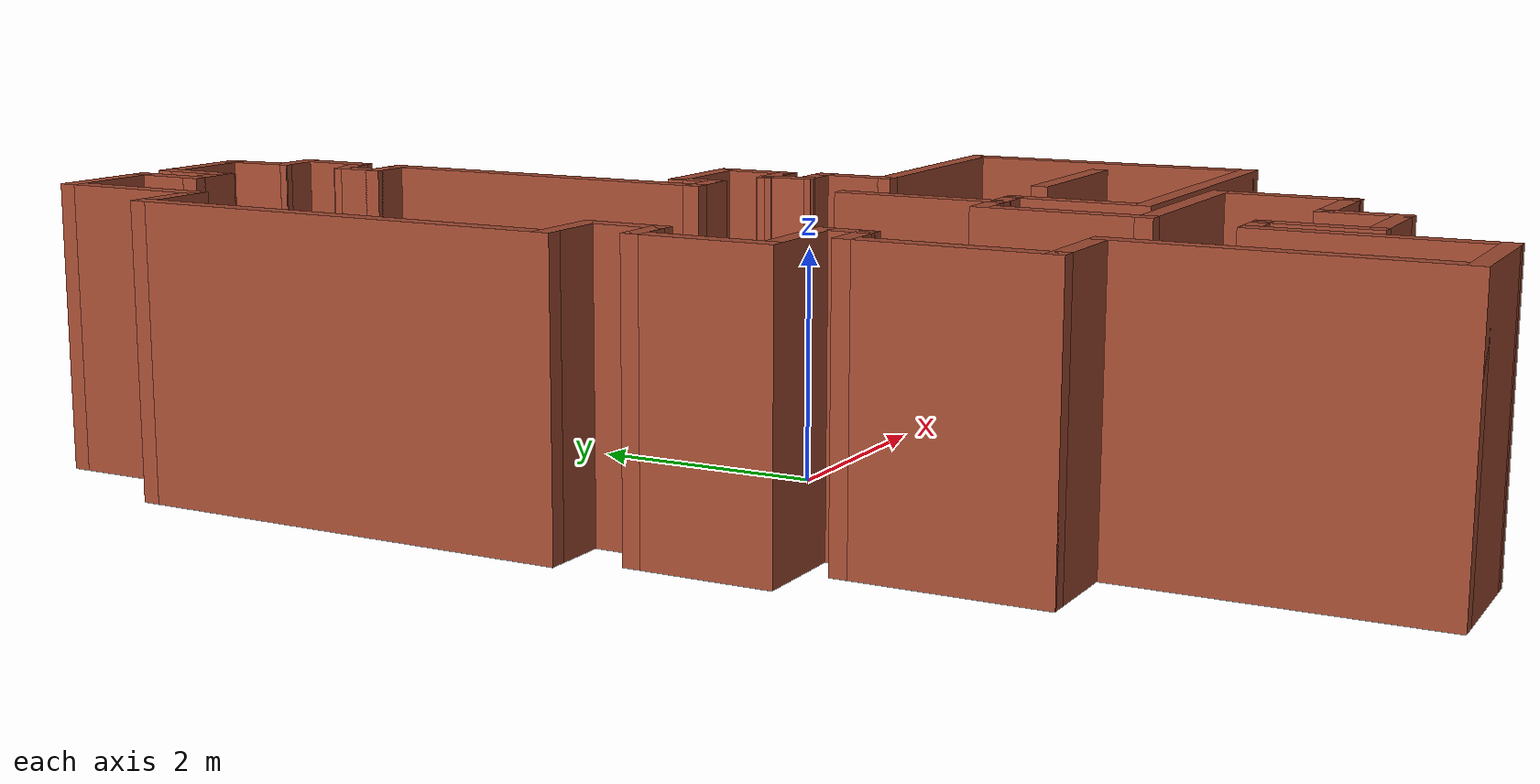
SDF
<?xml version='1.0'?>
<sdf version='1.6'>
  <model name='map_40'>
    <link name='Wall_0'>
      <pose frame=''>-1 5.72202 0 0 -0 3.14159</pose>
      <self_collide>0</self_collide>
      <enable_wind>0</enable_wind>
      <kinematic>0</kinematic>
      <visual name='Wall_0_Visual'>
        <pose frame=''>0 0 1.25 0 -0 0</pose>
        <geometry>
          <box>
            <size>1 0.15 2.5</size>
          </box>
        </geometry>
        <material>
          <script>
            <uri>file://media/materials/scripts/gazebo.material</uri>
            <name>Gazebo/Bricks</name>
          </script>
          <ambient>1 1 1 1</ambient>
          <shader type='pixel'/>
        </material>
        <meta>
          <layer>0</layer>
        </meta>
        <transparency>0</transparency>
        <cast_shadows>1</cast_shadows>
      </visual>
      <collision name='Wall_0_Collision'>
        <laser_retro>0</laser_retro>
        <max_contacts>10</max_contacts>
        <pose frame=''>0 0 1.25 0 -0 0</pose>
        <geometry>
          <box>
            <size>1 0.15 2.5</size>
          </box>
        </geometry>
        <surface>
          <friction>
            <ode>
              <mu>1</mu>
              <mu2>1</mu2>
              <fdir1>0 0 0</fdir1>
              <slip1>0</slip1>
              <slip2>0</slip2>
            </ode>
            <torsional>
              <coefficient>1</coefficient>
              <patch_radius>0</patch_radius>
              <surface_radius>0</surface_radius>
              <use_patch_radius>1</use_patch_radius>
              <ode>
                <slip>0</slip>
              </ode>
            </torsional>
          </friction>
          <bounce>
            <restitution_coefficient>0</restitution_coefficient>
            <threshold>1e+06</threshold>
          </bounce>
          <contact>
            <collide_without_contact>0</collide_without_contact>
            <collide_without_contact_bitmask>1</collide_without_contact_bitmask>
            <collide_bitmask>1</collide_bitmask>
            <ode>
              <soft_cfm>0</soft_cfm>
              <soft_erp>0.2</soft_erp>
              <kp>1e+13</kp>
              <kd>1</kd>
              <max_vel>0.01</max_vel>
              <min_depth>0</min_depth>
            </ode>
            <bullet>
              <split_impulse>1</split_impulse>
              <split_impulse_penetration_threshold>-0.01</split_impulse_penetration_threshold>
              <soft_cfm>0</soft_cfm>
              <soft_erp>0.2</soft_erp>
              <kp>1e+13</kp>
              <kd>1</kd>
            </bullet>
          </contact>
        </surface>
      </collision>
    </link>
    <link name='Wall_10'>
      <pose frame=''>-2.2 5.72202 0 0 -0 3.14159</pose>
      <self_collide>0</self_collide>
      <enable_wind>0</enable_wind>
      <kinematic>0</kinematic>
      <visual name='Wall_10_Visual'>
        <pose frame=''>0 0 1.25 0 -0 0</pose>
        <geometry>
          <box>
            <size>1 0.15 2.5</size>
          </box>
        </geometry>
        <material>
          <script>
            <uri>file://media/materials/scripts/gazebo.material</uri>
            <name>Gazebo/Bricks</name>
          </script>
          <ambient>1 1 1 1</ambient>
          <shader type='pixel'/>
        </material>
        <meta>
          <layer>0</layer>
        </meta>
        <transparency>0</transparency>
        <cast_shadows>1</cast_shadows>
      </visual>
      <collision name='Wall_10_Collision'>
        <laser_retro>0</laser_retro>
        <max_contacts>10</max_contacts>
        <pose frame=''>0 0 1.25 0 -0 0</pose>
        <geometry>
          <box>
            <size>1 0.15 2.5</size>
          </box>
        </geometry>
        <surface>
          <friction>
            <ode>
              <mu>1</mu>
              <mu2>1</mu2>
              <fdir1>0 0 0</fdir1>
              <slip1>0</slip1>
              <slip2>0</slip2>
            </ode>
            <torsional>
              <coefficient>1</coefficient>
              <patch_radius>0</patch_radius>
              <surface_radius>0</surface_radius>
              <use_patch_radius>1</use_patch_radius>
              <ode>
                <slip>0</slip>
              </ode>
            </torsional>
          </friction>
          <bounce>
            <restitution_coefficient>0</restitution_coefficient>
            <threshold>1e+06</threshold>
          </bounce>
          <contact>
            <collide_without_contact>0</collide_without_contact>
            <collide_without_contact_bitmask>1</collide_without_contact_bitmask>
            <collide_bitmask>1</collide_bitmask>
            <ode>
              <soft_cfm>0</soft_cfm>
              <soft_erp>0.2</soft_erp>
              <kp>1e+13</kp>
              <kd>1</kd>
              <max_vel>0.01</max_vel>
              <min_depth>0</min_depth>
            </ode>
            <bullet>
              <split_impulse>1</split_impulse>
              <split_impulse_penetration_threshold>-0.01</split_impulse_penetration_threshold>
              <soft_cfm>0</soft_cfm>
              <soft_erp>0.2</soft_erp>
              <kp>1e+13</kp>
              <kd>1</kd>
            </bullet>
          </contact>
        </surface>
      </collision>
    </link>
    <link name='Wall_11'>
      <pose frame=''>-2.625 5.04702 0 0 0 -1.5708</pose>
      <self_collide>0</self_collide>
      <enable_wind>0</enable_wind>
      <kinematic>0</kinematic>
      <visual name='Wall_11_Visual'>
        <pose frame=''>0 0 1.25 0 -0 0</pose>
        <geometry>
          <box>
            <size>1.5 0.15 2.5</size>
          </box>
        </geometry>
        <material>
          <script>
            <uri>file://media/materials/scripts/gazebo.material</uri>
            <name>Gazebo/Bricks</name>
          </script>
          <ambient>1 1 1 1</ambient>
          <shader type='pixel'/>
        </material>
        <meta>
          <layer>0</layer>
        </meta>
        <transparency>0</transparency>
        <cast_shadows>1</cast_shadows>
      </visual>
      <collision name='Wall_11_Collision'>
        <laser_retro>0</laser_retro>
        <max_contacts>10</max_contacts>
        <pose frame=''>0 0 1.25 0 -0 0</pose>
        <geometry>
          <box>
            <size>1.5 0.15 2.5</size>
          </box>
        </geometry>
        <surface>
          <friction>
            <ode>
              <mu>1</mu>
              <mu2>1</mu2>
              <fdir1>0 0 0</fdir1>
              <slip1>0</slip1>
              <slip2>0</slip2>
            </ode>
            <torsional>
              <coefficient>1</coefficient>
              <patch_radius>0</patch_radius>
              <surface_radius>0</surface_radius>
              <use_patch_radius>1</use_patch_radius>
              <ode>
                <slip>0</slip>
              </ode>
            </torsional>
          </friction>
          <bounce>
            <restitution_coefficient>0</restitution_coefficient>
            <threshold>1e+06</threshold>
          </bounce>
          <contact>
            <collide_without_contact>0</collide_without_contact>
            <collide_without_contact_bitmask>1</collide_without_contact_bitmask>
            <collide_bitmask>1</collide_bitmask>
            <ode>
              <soft_cfm>0</soft_cfm>
              <soft_erp>0.2</soft_erp>
              <kp>1e+13</kp>
              <kd>1</kd>
              <max_vel>0.01</max_vel>
              <min_depth>0</min_depth>
            </ode>
            <bullet>
              <split_impulse>1</split_impulse>
              <split_impulse_penetration_threshold>-0.01</split_impulse_penetration_threshold>
              <soft_cfm>0</soft_cfm>
              <soft_erp>0.2</soft_erp>
              <kp>1e+13</kp>
              <kd>1</kd>
            </bullet>
          </contact>
        </surface>
      </collision>
    </link>
    <link name='Wall_12'>
      <pose frame=''>-2.925 4.37202 0 0 -0 3.14159</pose>
      <self_collide>0</self_collide>
      <enable_wind>0</enable_wind>
      <kinematic>0</kinematic>
      <visual name='Wall_12_Visual'>
        <pose frame=''>0 0 1.25 0 -0 0</pose>
        <geometry>
          <box>
            <size>0.75 0.15 2.5</size>
          </box>
        </geometry>
        <material>
          <script>
            <uri>file://media/materials/scripts/gazebo.material</uri>
            <name>Gazebo/Bricks</name>
          </script>
          <ambient>1 1 1 1</ambient>
          <shader type='pixel'/>
        </material>
        <meta>
          <layer>0</layer>
        </meta>
        <transparency>0</transparency>
        <cast_shadows>1</cast_shadows>
      </visual>
      <collision name='Wall_12_Collision'>
        <laser_retro>0</laser_retro>
        <max_contacts>10</max_contacts>
        <pose frame=''>0 0 1.25 0 -0 0</pose>
        <geometry>
          <box>
            <size>0.75 0.15 2.5</size>
          </box>
        </geometry>
        <surface>
          <friction>
            <ode>
              <mu>1</mu>
              <mu2>1</mu2>
              <fdir1>0 0 0</fdir1>
              <slip1>0</slip1>
              <slip2>0</slip2>
            </ode>
            <torsional>
              <coefficient>1</coefficient>
              <patch_radius>0</patch_radius>
              <surface_radius>0</surface_radius>
              <use_patch_radius>1</use_patch_radius>
              <ode>
                <slip>0</slip>
              </ode>
            </torsional>
          </friction>
          <bounce>
            <restitution_coefficient>0</restitution_coefficient>
            <threshold>1e+06</threshold>
          </bounce>
          <contact>
            <collide_without_contact>0</collide_without_contact>
            <collide_without_contact_bitmask>1</collide_without_contact_bitmask>
            <collide_bitmask>1</collide_bitmask>
            <ode>
              <soft_cfm>0</soft_cfm>
              <soft_erp>0.2</soft_erp>
              <kp>1e+13</kp>
              <kd>1</kd>
              <max_vel>0.01</max_vel>
              <min_depth>0</min_depth>
            </ode>
            <bullet>
              <split_impulse>1</split_impulse>
              <split_impulse_penetration_threshold>-0.01</split_impulse_penetration_threshold>
              <soft_cfm>0</soft_cfm>
              <soft_erp>0.2</soft_erp>
              <kp>1e+13</kp>
              <kd>1</kd>
            </bullet>
          </contact>
        </surface>
      </collision>
    </link>
    <link name='Wall_13'>
      <pose frame=''>-3.225 2.44702 0 0 0 -1.5708</pose>
      <self_collide>0</self_collide>
      <enable_wind>0</enable_wind>
      <kinematic>0</kinematic>
      <visual name='Wall_13_Visual'>
        <pose frame=''>0 0 1.25 0 -0 0</pose>
        <geometry>
          <box>
            <size>4 0.15 2.5</size>
          </box>
        </geometry>
        <material>
          <script>
            <uri>file://media/materials/scripts/gazebo.material</uri>
            <name>Gazebo/Bricks</name>
          </script>
          <ambient>1 1 1 1</ambient>
          <shader type='pixel'/>
        </material>
        <meta>
          <layer>0</layer>
        </meta>
        <transparency>0</transparency>
        <cast_shadows>1</cast_shadows>
      </visual>
      <collision name='Wall_13_Collision'>
        <laser_retro>0</laser_retro>
        <max_contacts>10</max_contacts>
        <pose frame=''>0 0 1.25 0 -0 0</pose>
        <geometry>
          <box>
            <size>4 0.15 2.5</size>
          </box>
        </geometry>
        <surface>
          <friction>
            <ode>
              <mu>1</mu>
              <mu2>1</mu2>
              <fdir1>0 0 0</fdir1>
              <slip1>0</slip1>
              <slip2>0</slip2>
            </ode>
            <torsional>
              <coefficient>1</coefficient>
              <patch_radius>0</patch_radius>
              <surface_radius>0</surface_radius>
              <use_patch_radius>1</use_patch_radius>
              <ode>
                <slip>0</slip>
              </ode>
            </torsional>
          </friction>
          <bounce>
            <restitution_coefficient>0</restitution_coefficient>
            <threshold>1e+06</threshold>
          </bounce>
          <contact>
            <collide_without_contact>0</collide_without_contact>
            <collide_without_contact_bitmask>1</collide_without_contact_bitmask>
            <collide_bitmask>1</collide_bitmask>
            <ode>
              <soft_cfm>0</soft_cfm>
              <soft_erp>0.2</soft_erp>
              <kp>1e+13</kp>
              <kd>1</kd>
              <max_vel>0.01</max_vel>
              <min_depth>0</min_depth>
            </ode>
            <bullet>
              <split_impulse>1</split_impulse>
              <split_impulse_penetration_threshold>-0.01</split_impulse_penetration_threshold>
              <soft_cfm>0</soft_cfm>
              <soft_erp>0.2</soft_erp>
              <kp>1e+13</kp>
              <kd>1</kd>
            </bullet>
          </contact>
        </surface>
      </collision>
    </link>
    <link name='Wall_16'>
      <pose frame=''>-2.925 0.522023 0 0 -0 0</pose>
      <self_collide>0</self_collide>
      <enable_wind>0</enable_wind>
      <kinematic>0</kinematic>
      <visual name='Wall_16_Visual'>
        <pose frame=''>0 0 1.25 0 -0 0</pose>
        <geometry>
          <box>
            <size>0.75 0.15 2.5</size>
          </box>
        </geometry>
        <material>
          <script>
            <uri>file://media/materials/scripts/gazebo.material</uri>
            <name>Gazebo/Bricks</name>
          </script>
          <ambient>1 1 1 1</ambient>
          <shader type='pixel'/>
        </material>
        <meta>
          <layer>0</layer>
        </meta>
        <transparency>0</transparency>
        <cast_shadows>1</cast_shadows>
      </visual>
      <collision name='Wall_16_Collision'>
        <laser_retro>0</laser_retro>
        <max_contacts>10</max_contacts>
        <pose frame=''>0 0 1.25 0 -0 0</pose>
        <geometry>
          <box>
            <size>0.75 0.15 2.5</size>
          </box>
        </geometry>
        <surface>
          <friction>
            <ode>
              <mu>1</mu>
              <mu2>1</mu2>
              <fdir1>0 0 0</fdir1>
              <slip1>0</slip1>
              <slip2>0</slip2>
            </ode>
            <torsional>
              <coefficient>1</coefficient>
              <patch_radius>0</patch_radius>
              <surface_radius>0</surface_radius>
              <use_patch_radius>1</use_patch_radius>
              <ode>
                <slip>0</slip>
              </ode>
            </torsional>
          </friction>
          <bounce>
            <restitution_coefficient>0</restitution_coefficient>
            <threshold>1e+06</threshold>
          </bounce>
          <contact>
            <collide_without_contact>0</collide_without_contact>
            <collide_without_contact_bitmask>1</collide_without_contact_bitmask>
            <collide_bitmask>1</collide_bitmask>
            <ode>
              <soft_cfm>0</soft_cfm>
              <soft_erp>0.2</soft_erp>
              <kp>1e+13</kp>
              <kd>1</kd>
              <max_vel>0.01</max_vel>
              <min_depth>0</min_depth>
            </ode>
            <bullet>
              <split_impulse>1</split_impulse>
              <split_impulse_penetration_threshold>-0.01</split_impulse_penetration_threshold>
              <soft_cfm>0</soft_cfm>
              <soft_erp>0.2</soft_erp>
              <kp>1e+13</kp>
              <kd>1</kd>
            </bullet>
          </contact>
        </surface>
      </collision>
    </link>
    <link name='Wall_17'>
      <pose frame=''>-2.625 0.222023 0 0 0 -1.5708</pose>
      <self_collide>0</self_collide>
      <enable_wind>0</enable_wind>
      <kinematic>0</kinematic>
      <visual name='Wall_17_Visual'>
        <pose frame=''>0 0 1.25 0 -0 0</pose>
        <geometry>
          <box>
            <size>0.75 0.15 2.5</size>
          </box>
        </geometry>
        <material>
          <script>
            <uri>file://media/materials/scripts/gazebo.material</uri>
            <name>Gazebo/Bricks</name>
          </script>
          <ambient>1 1 1 1</ambient>
          <shader type='pixel'/>
        </material>
        <meta>
          <layer>0</layer>
        </meta>
        <transparency>0</transparency>
        <cast_shadows>1</cast_shadows>
      </visual>
      <collision name='Wall_17_Collision'>
        <laser_retro>0</laser_retro>
        <max_contacts>10</max_contacts>
        <pose frame=''>0 0 1.25 0 -0 0</pose>
        <geometry>
          <box>
            <size>0.75 0.15 2.5</size>
          </box>
        </geometry>
        <surface>
          <friction>
            <ode>
              <mu>1</mu>
              <mu2>1</mu2>
              <fdir1>0 0 0</fdir1>
              <slip1>0</slip1>
              <slip2>0</slip2>
            </ode>
            <torsional>
              <coefficient>1</coefficient>
              <patch_radius>0</patch_radius>
              <surface_radius>0</surface_radius>
              <use_patch_radius>1</use_patch_radius>
              <ode>
                <slip>0</slip>
              </ode>
            </torsional>
          </friction>
          <bounce>
            <restitution_coefficient>0</restitution_coefficient>
            <threshold>1e+06</threshold>
          </bounce>
          <contact>
            <collide_without_contact>0</collide_without_contact>
            <collide_without_contact_bitmask>1</collide_without_contact_bitmask>
            <collide_bitmask>1</collide_bitmask>
            <ode>
              <soft_cfm>0</soft_cfm>
              <soft_erp>0.2</soft_erp>
              <kp>1e+13</kp>
              <kd>1</kd>
              <max_vel>0.01</max_vel>
              <min_depth>0</min_depth>
            </ode>
            <bullet>
              <split_impulse>1</split_impulse>
              <split_impulse_penetration_threshold>-0.01</split_impulse_penetration_threshold>
              <soft_cfm>0</soft_cfm>
              <soft_erp>0.2</soft_erp>
              <kp>1e+13</kp>
              <kd>1</kd>
            </bullet>
          </contact>
        </surface>
      </collision>
    </link>
    <link name='Wall_18'>
      <pose frame=''>-2.8 -0.077977 0 0 -0 3.14159</pose>
      <self_collide>0</self_collide>
      <enable_wind>0</enable_wind>
      <kinematic>0</kinematic>
      <visual name='Wall_18_Visual'>
        <pose frame=''>0 0 1.25 0 -0 0</pose>
        <geometry>
          <box>
            <size>0.5 0.15 2.5</size>
          </box>
        </geometry>
        <material>
          <script>
            <uri>file://media/materials/scripts/gazebo.material</uri>
            <name>Gazebo/Bricks</name>
          </script>
          <ambient>1 1 1 1</ambient>
          <shader type='pixel'/>
        </material>
        <meta>
          <layer>0</layer>
        </meta>
        <transparency>0</transparency>
        <cast_shadows>1</cast_shadows>
      </visual>
      <collision name='Wall_18_Collision'>
        <laser_retro>0</laser_retro>
        <max_contacts>10</max_contacts>
        <pose frame=''>0 0 1.25 0 -0 0</pose>
        <geometry>
          <box>
            <size>0.5 0.15 2.5</size>
          </box>
        </geometry>
        <surface>
          <friction>
            <ode>
              <mu>1</mu>
              <mu2>1</mu2>
              <fdir1>0 0 0</fdir1>
              <slip1>0</slip1>
              <slip2>0</slip2>
            </ode>
            <torsional>
              <coefficient>1</coefficient>
              <patch_radius>0</patch_radius>
              <surface_radius>0</surface_radius>
              <use_patch_radius>1</use_patch_radius>
              <ode>
                <slip>0</slip>
              </ode>
            </torsional>
          </friction>
          <bounce>
            <restitution_coefficient>0</restitution_coefficient>
            <threshold>1e+06</threshold>
          </bounce>
          <contact>
            <collide_without_contact>0</collide_without_contact>
            <collide_without_contact_bitmask>1</collide_without_contact_bitmask>
            <collide_bitmask>1</collide_bitmask>
            <ode>
              <soft_cfm>0</soft_cfm>
              <soft_erp>0.2</soft_erp>
              <kp>1e+13</kp>
              <kd>1</kd>
              <max_vel>0.01</max_vel>
              <min_depth>0</min_depth>
            </ode>
            <bullet>
              <split_impulse>1</split_impulse>
              <split_impulse_penetration_threshold>-0.01</split_impulse_penetration_threshold>
              <soft_cfm>0</soft_cfm>
              <soft_erp>0.2</soft_erp>
              <kp>1e+13</kp>
              <kd>1</kd>
            </bullet>
          </contact>
        </surface>
      </collision>
    </link>
    <link name='Wall_19'>
      <pose frame=''>-2.975 -0.627977 0 0 0 -1.5708</pose>
      <self_collide>0</self_collide>
      <enable_wind>0</enable_wind>
      <kinematic>0</kinematic>
      <visual name='Wall_19_Visual'>
        <pose frame=''>0 0 1.25 0 -0 0</pose>
        <geometry>
          <box>
            <size>1.25 0.15 2.5</size>
          </box>
        </geometry>
        <material>
          <script>
            <uri>file://media/materials/scripts/gazebo.material</uri>
            <name>Gazebo/Bricks</name>
          </script>
          <ambient>1 1 1 1</ambient>
          <shader type='pixel'/>
        </material>
        <meta>
          <layer>0</layer>
        </meta>
        <transparency>0</transparency>
        <cast_shadows>1</cast_shadows>
      </visual>
      <collision name='Wall_19_Collision'>
        <laser_retro>0</laser_retro>
        <max_contacts>10</max_contacts>
        <pose frame=''>0 0 1.25 0 -0 0</pose>
        <geometry>
          <box>
            <size>1.25 0.15 2.5</size>
          </box>
        </geometry>
        <surface>
          <friction>
            <ode>
              <mu>1</mu>
              <mu2>1</mu2>
              <fdir1>0 0 0</fdir1>
              <slip1>0</slip1>
              <slip2>0</slip2>
            </ode>
            <torsional>
              <coefficient>1</coefficient>
              <patch_radius>0</patch_radius>
              <surface_radius>0</surface_radius>
              <use_patch_radius>1</use_patch_radius>
              <ode>
                <slip>0</slip>
              </ode>
            </torsional>
          </friction>
          <bounce>
            <restitution_coefficient>0</restitution_coefficient>
            <threshold>1e+06</threshold>
          </bounce>
          <contact>
            <collide_without_contact>0</collide_without_contact>
            <collide_without_contact_bitmask>1</collide_without_contact_bitmask>
            <collide_bitmask>1</collide_bitmask>
            <ode>
              <soft_cfm>0</soft_cfm>
              <soft_erp>0.2</soft_erp>
              <kp>1e+13</kp>
              <kd>1</kd>
              <max_vel>0.01</max_vel>
              <min_depth>0</min_depth>
            </ode>
            <bullet>
              <split_impulse>1</split_impulse>
              <split_impulse_penetration_threshold>-0.01</split_impulse_penetration_threshold>
              <soft_cfm>0</soft_cfm>
              <soft_erp>0.2</soft_erp>
              <kp>1e+13</kp>
              <kd>1</kd>
            </bullet>
          </contact>
        </surface>
      </collision>
    </link>
    <link name='Wall_20'>
      <pose frame=''>-2.55 -1.17798 0 0 -0 0</pose>
      <self_collide>0</self_collide>
      <enable_wind>0</enable_wind>
      <kinematic>0</kinematic>
      <visual name='Wall_20_Visual'>
        <pose frame=''>0 0 1.25 0 -0 0</pose>
        <geometry>
          <box>
            <size>1 0.15 2.5</size>
          </box>
        </geometry>
        <material>
          <script>
            <uri>file://media/materials/scripts/gazebo.material</uri>
            <name>Gazebo/Bricks</name>
          </script>
          <ambient>1 1 1 1</ambient>
          <shader type='pixel'/>
        </material>
        <meta>
          <layer>0</layer>
        </meta>
        <transparency>0</transparency>
        <cast_shadows>1</cast_shadows>
      </visual>
      <collision name='Wall_20_Collision'>
        <laser_retro>0</laser_retro>
        <max_contacts>10</max_contacts>
        <pose frame=''>0 0 1.25 0 -0 0</pose>
        <geometry>
          <box>
            <size>1 0.15 2.5</size>
          </box>
        </geometry>
        <surface>
          <friction>
            <ode>
              <mu>1</mu>
              <mu2>1</mu2>
              <fdir1>0 0 0</fdir1>
              <slip1>0</slip1>
              <slip2>0</slip2>
            </ode>
            <torsional>
              <coefficient>1</coefficient>
              <patch_radius>0</patch_radius>
              <surface_radius>0</surface_radius>
              <use_patch_radius>1</use_patch_radius>
              <ode>
                <slip>0</slip>
              </ode>
            </torsional>
          </friction>
          <bounce>
            <restitution_coefficient>0</restitution_coefficient>
            <threshold>1e+06</threshold>
          </bounce>
          <contact>
            <collide_without_contact>0</collide_without_contact>
            <collide_without_contact_bitmask>1</collide_without_contact_bitmask>
            <collide_bitmask>1</collide_bitmask>
            <ode>
              <soft_cfm>0</soft_cfm>
              <soft_erp>0.2</soft_erp>
              <kp>1e+13</kp>
              <kd>1</kd>
              <max_vel>0.01</max_vel>
              <min_depth>0</min_depth>
            </ode>
            <bullet>
              <split_impulse>1</split_impulse>
              <split_impulse_penetration_threshold>-0.01</split_impulse_penetration_threshold>
              <soft_cfm>0</soft_cfm>
              <soft_erp>0.2</soft_erp>
              <kp>1e+13</kp>
              <kd>1</kd>
            </bullet>
          </contact>
        </surface>
      </collision>
    </link>
    <link name='Wall_21'>
      <pose frame=''>-2.125 -1.35298 0 0 0 -1.5708</pose>
      <self_collide>0</self_collide>
      <enable_wind>0</enable_wind>
      <kinematic>0</kinematic>
      <visual name='Wall_21_Visual'>
        <pose frame=''>0 0 1.25 0 -0 0</pose>
        <geometry>
          <box>
            <size>0.5 0.15 2.5</size>
          </box>
        </geometry>
        <material>
          <script>
            <uri>file://media/materials/scripts/gazebo.material</uri>
            <name>Gazebo/Bricks</name>
          </script>
          <ambient>1 1 1 1</ambient>
          <shader type='pixel'/>
        </material>
        <meta>
          <layer>0</layer>
        </meta>
        <transparency>0</transparency>
        <cast_shadows>1</cast_shadows>
      </visual>
      <collision name='Wall_21_Collision'>
        <laser_retro>0</laser_retro>
        <max_contacts>10</max_contacts>
        <pose frame=''>0 0 1.25 0 -0 0</pose>
        <geometry>
          <box>
            <size>0.5 0.15 2.5</size>
          </box>
        </geometry>
        <surface>
          <friction>
            <ode>
              <mu>1</mu>
              <mu2>1</mu2>
              <fdir1>0 0 0</fdir1>
              <slip1>0</slip1>
              <slip2>0</slip2>
            </ode>
            <torsional>
              <coefficient>1</coefficient>
              <patch_radius>0</patch_radius>
              <surface_radius>0</surface_radius>
              <use_patch_radius>1</use_patch_radius>
              <ode>
                <slip>0</slip>
              </ode>
            </torsional>
          </friction>
          <bounce>
            <restitution_coefficient>0</restitution_coefficient>
            <threshold>1e+06</threshold>
          </bounce>
          <contact>
            <collide_without_contact>0</collide_without_contact>
            <collide_without_contact_bitmask>1</collide_without_contact_bitmask>
            <collide_bitmask>1</collide_bitmask>
            <ode>
              <soft_cfm>0</soft_cfm>
              <soft_erp>0.2</soft_erp>
              <kp>1e+13</kp>
              <kd>1</kd>
              <max_vel>0.01</max_vel>
              <min_depth>0</min_depth>
            </ode>
            <bullet>
              <split_impulse>1</split_impulse>
              <split_impulse_penetration_threshold>-0.01</split_impulse_penetration_threshold>
              <soft_cfm>0</soft_cfm>
              <soft_erp>0.2</soft_erp>
              <kp>1e+13</kp>
              <kd>1</kd>
            </bullet>
          </contact>
        </surface>
      </collision>
    </link>
    <link name='Wall_22'>
      <pose frame=''>-2.3 -1.52798 0 0 -0 3.14159</pose>
      <self_collide>0</self_collide>
      <enable_wind>0</enable_wind>
      <kinematic>0</kinematic>
      <visual name='Wall_22_Visual'>
        <pose frame=''>0 0 1.25 0 -0 0</pose>
        <geometry>
          <box>
            <size>0.5 0.15 2.5</size>
          </box>
        </geometry>
        <material>
          <script>
            <uri>file://media/materials/scripts/gazebo.material</uri>
            <name>Gazebo/Bricks</name>
          </script>
          <ambient>1 1 1 1</ambient>
          <shader type='pixel'/>
        </material>
        <meta>
          <layer>0</layer>
        </meta>
        <transparency>0</transparency>
        <cast_shadows>1</cast_shadows>
      </visual>
      <collision name='Wall_22_Collision'>
        <laser_retro>0</laser_retro>
        <max_contacts>10</max_contacts>
        <pose frame=''>0 0 1.25 0 -0 0</pose>
        <geometry>
          <box>
            <size>0.5 0.15 2.5</size>
          </box>
        </geometry>
        <surface>
          <friction>
            <ode>
              <mu>1</mu>
              <mu2>1</mu2>
              <fdir1>0 0 0</fdir1>
              <slip1>0</slip1>
              <slip2>0</slip2>
            </ode>
            <torsional>
              <coefficient>1</coefficient>
              <patch_radius>0</patch_radius>
              <surface_radius>0</surface_radius>
              <use_patch_radius>1</use_patch_radius>
              <ode>
                <slip>0</slip>
              </ode>
            </torsional>
          </friction>
          <bounce>
            <restitution_coefficient>0</restitution_coefficient>
            <threshold>1e+06</threshold>
          </bounce>
          <contact>
            <collide_without_contact>0</collide_without_contact>
            <collide_without_contact_bitmask>1</collide_without_contact_bitmask>
            <collide_bitmask>1</collide_bitmask>
            <ode>
              <soft_cfm>0</soft_cfm>
              <soft_erp>0.2</soft_erp>
              <kp>1e+13</kp>
              <kd>1</kd>
              <max_vel>0.01</max_vel>
              <min_depth>0</min_depth>
            </ode>
            <bullet>
              <split_impulse>1</split_impulse>
              <split_impulse_penetration_threshold>-0.01</split_impulse_penetration_threshold>
              <soft_cfm>0</soft_cfm>
              <soft_erp>0.2</soft_erp>
              <kp>1e+13</kp>
              <kd>1</kd>
            </bullet>
          </contact>
        </surface>
      </collision>
    </link>
    <link name='Wall_23'>
      <pose frame=''>-2.475 -2.32798 0 0 0 -1.5708</pose>
      <self_collide>0</self_collide>
      <enable_wind>0</enable_wind>
      <kinematic>0</kinematic>
      <visual name='Wall_23_Visual'>
        <pose frame=''>0 0 1.25 0 -0 0</pose>
        <geometry>
          <box>
            <size>1.75 0.15 2.5</size>
          </box>
        </geometry>
        <material>
          <script>
            <uri>file://media/materials/scripts/gazebo.material</uri>
            <name>Gazebo/Bricks</name>
          </script>
          <ambient>1 1 1 1</ambient>
          <shader type='pixel'/>
        </material>
        <meta>
          <layer>0</layer>
        </meta>
        <transparency>0</transparency>
        <cast_shadows>1</cast_shadows>
      </visual>
      <collision name='Wall_23_Collision'>
        <laser_retro>0</laser_retro>
        <max_contacts>10</max_contacts>
        <pose frame=''>0 0 1.25 0 -0 0</pose>
        <geometry>
          <box>
            <size>1.75 0.15 2.5</size>
          </box>
        </geometry>
        <surface>
          <friction>
            <ode>
              <mu>1</mu>
              <mu2>1</mu2>
              <fdir1>0 0 0</fdir1>
              <slip1>0</slip1>
              <slip2>0</slip2>
            </ode>
            <torsional>
              <coefficient>1</coefficient>
              <patch_radius>0</patch_radius>
              <surface_radius>0</surface_radius>
              <use_patch_radius>1</use_patch_radius>
              <ode>
                <slip>0</slip>
              </ode>
            </torsional>
          </friction>
          <bounce>
            <restitution_coefficient>0</restitution_coefficient>
            <threshold>1e+06</threshold>
          </bounce>
          <contact>
            <collide_without_contact>0</collide_without_contact>
            <collide_without_contact_bitmask>1</collide_without_contact_bitmask>
            <collide_bitmask>1</collide_bitmask>
            <ode>
              <soft_cfm>0</soft_cfm>
              <soft_erp>0.2</soft_erp>
              <kp>1e+13</kp>
              <kd>1</kd>
              <max_vel>0.01</max_vel>
              <min_depth>0</min_depth>
            </ode>
            <bullet>
              <split_impulse>1</split_impulse>
              <split_impulse_penetration_threshold>-0.01</split_impulse_penetration_threshold>
              <soft_cfm>0</soft_cfm>
              <soft_erp>0.2</soft_erp>
              <kp>1e+13</kp>
              <kd>1</kd>
            </bullet>
          </contact>
        </surface>
      </collision>
    </link>
    <link name='Wall_24'>
      <pose frame=''>-2.05 -3.12798 0 0 -0 0</pose>
      <self_collide>0</self_collide>
      <enable_wind>0</enable_wind>
      <kinematic>0</kinematic>
      <visual name='Wall_24_Visual'>
        <pose frame=''>0 0 1.25 0 -0 0</pose>
        <geometry>
          <box>
            <size>1 0.15 2.5</size>
          </box>
        </geometry>
        <material>
          <script>
            <uri>file://media/materials/scripts/gazebo.material</uri>
            <name>Gazebo/Bricks</name>
          </script>
          <ambient>1 1 1 1</ambient>
          <shader type='pixel'/>
        </material>
        <meta>
          <layer>0</layer>
        </meta>
        <transparency>0</transparency>
        <cast_shadows>1</cast_shadows>
      </visual>
      <collision name='Wall_24_Collision'>
        <laser_retro>0</laser_retro>
        <max_contacts>10</max_contacts>
        <pose frame=''>0 0 1.25 0 -0 0</pose>
        <geometry>
          <box>
            <size>1 0.15 2.5</size>
          </box>
        </geometry>
        <surface>
          <friction>
            <ode>
              <mu>1</mu>
              <mu2>1</mu2>
              <fdir1>0 0 0</fdir1>
              <slip1>0</slip1>
              <slip2>0</slip2>
            </ode>
            <torsional>
              <coefficient>1</coefficient>
              <patch_radius>0</patch_radius>
              <surface_radius>0</surface_radius>
              <use_patch_radius>1</use_patch_radius>
              <ode>
                <slip>0</slip>
              </ode>
            </torsional>
          </friction>
          <bounce>
            <restitution_coefficient>0</restitution_coefficient>
            <threshold>1e+06</threshold>
          </bounce>
          <contact>
            <collide_without_contact>0</collide_without_contact>
            <collide_without_contact_bitmask>1</collide_without_contact_bitmask>
            <collide_bitmask>1</collide_bitmask>
            <ode>
              <soft_cfm>0</soft_cfm>
              <soft_erp>0.2</soft_erp>
              <kp>1e+13</kp>
              <kd>1</kd>
              <max_vel>0.01</max_vel>
              <min_depth>0</min_depth>
            </ode>
            <bullet>
              <split_impulse>1</split_impulse>
              <split_impulse_penetration_threshold>-0.01</split_impulse_penetration_threshold>
              <soft_cfm>0</soft_cfm>
              <soft_erp>0.2</soft_erp>
              <kp>1e+13</kp>
              <kd>1</kd>
            </bullet>
          </contact>
        </surface>
      </collision>
    </link>
    <link name='Wall_25'>
      <pose frame=''>-1.625 -4.42798 0 0 0 -1.5708</pose>
      <self_collide>0</self_collide>
      <enable_wind>0</enable_wind>
      <kinematic>0</kinematic>
      <visual name='Wall_25_Visual'>
        <pose frame=''>0 0 1.25 0 -0 0</pose>
        <geometry>
          <box>
            <size>2.75 0.15 2.5</size>
          </box>
        </geometry>
        <material>
          <script>
            <uri>file://media/materials/scripts/gazebo.material</uri>
            <name>Gazebo/Bricks</name>
          </script>
          <ambient>1 1 1 1</ambient>
          <shader type='pixel'/>
        </material>
        <meta>
          <layer>0</layer>
        </meta>
        <transparency>0</transparency>
        <cast_shadows>1</cast_shadows>
      </visual>
      <collision name='Wall_25_Collision'>
        <laser_retro>0</laser_retro>
        <max_contacts>10</max_contacts>
        <pose frame=''>0 0 1.25 0 -0 0</pose>
        <geometry>
          <box>
            <size>2.75 0.15 2.5</size>
          </box>
        </geometry>
        <surface>
          <friction>
            <ode>
              <mu>1</mu>
              <mu2>1</mu2>
              <fdir1>0 0 0</fdir1>
              <slip1>0</slip1>
              <slip2>0</slip2>
            </ode>
            <torsional>
              <coefficient>1</coefficient>
              <patch_radius>0</patch_radius>
              <surface_radius>0</surface_radius>
              <use_patch_radius>1</use_patch_radius>
              <ode>
                <slip>0</slip>
              </ode>
            </torsional>
          </friction>
          <bounce>
            <restitution_coefficient>0</restitution_coefficient>
            <threshold>1e+06</threshold>
          </bounce>
          <contact>
            <collide_without_contact>0</collide_without_contact>
            <collide_without_contact_bitmask>1</collide_without_contact_bitmask>
            <collide_bitmask>1</collide_bitmask>
            <ode>
              <soft_cfm>0</soft_cfm>
              <soft_erp>0.2</soft_erp>
              <kp>1e+13</kp>
              <kd>1</kd>
              <max_vel>0.01</max_vel>
              <min_depth>0</min_depth>
            </ode>
            <bullet>
              <split_impulse>1</split_impulse>
              <split_impulse_penetration_threshold>-0.01</split_impulse_penetration_threshold>
              <soft_cfm>0</soft_cfm>
              <soft_erp>0.2</soft_erp>
              <kp>1e+13</kp>
              <kd>1</kd>
            </bullet>
          </contact>
        </surface>
      </collision>
    </link>
    <link name='Wall_26'>
      <pose frame=''>-1.075 -5.72798 0 0 -0 0</pose>
      <self_collide>0</self_collide>
      <enable_wind>0</enable_wind>
      <kinematic>0</kinematic>
      <visual name='Wall_26_Visual'>
        <pose frame=''>0 0 1.25 0 -0 0</pose>
        <geometry>
          <box>
            <size>1.25 0.15 2.5</size>
          </box>
        </geometry>
        <material>
          <script>
            <uri>file://media/materials/scripts/gazebo.material</uri>
            <name>Gazebo/Bricks</name>
          </script>
          <ambient>1 1 1 1</ambient>
          <shader type='pixel'/>
        </material>
        <meta>
          <layer>0</layer>
        </meta>
        <transparency>0</transparency>
        <cast_shadows>1</cast_shadows>
      </visual>
      <collision name='Wall_26_Collision'>
        <laser_retro>0</laser_retro>
        <max_contacts>10</max_contacts>
        <pose frame=''>0 0 1.25 0 -0 0</pose>
        <geometry>
          <box>
            <size>1.25 0.15 2.5</size>
          </box>
        </geometry>
        <surface>
          <friction>
            <ode>
              <mu>1</mu>
              <mu2>1</mu2>
              <fdir1>0 0 0</fdir1>
              <slip1>0</slip1>
              <slip2>0</slip2>
            </ode>
            <torsional>
              <coefficient>1</coefficient>
              <patch_radius>0</patch_radius>
              <surface_radius>0</surface_radius>
              <use_patch_radius>1</use_patch_radius>
              <ode>
                <slip>0</slip>
              </ode>
            </torsional>
          </friction>
          <bounce>
            <restitution_coefficient>0</restitution_coefficient>
            <threshold>1e+06</threshold>
          </bounce>
          <contact>
            <collide_without_contact>0</collide_without_contact>
            <collide_without_contact_bitmask>1</collide_without_contact_bitmask>
            <collide_bitmask>1</collide_bitmask>
            <ode>
              <soft_cfm>0</soft_cfm>
              <soft_erp>0.2</soft_erp>
              <kp>1e+13</kp>
              <kd>1</kd>
              <max_vel>0.01</max_vel>
              <min_depth>0</min_depth>
            </ode>
            <bullet>
              <split_impulse>1</split_impulse>
              <split_impulse_penetration_threshold>-0.01</split_impulse_penetration_threshold>
              <soft_cfm>0</soft_cfm>
              <soft_erp>0.2</soft_erp>
              <kp>1e+13</kp>
              <kd>1</kd>
            </bullet>
          </contact>
        </surface>
      </collision>
    </link>
    <link name='Wall_27'>
      <pose frame=''>-0.525 -4.80298 0 0 -0 1.5708</pose>
      <self_collide>0</self_collide>
      <enable_wind>0</enable_wind>
      <kinematic>0</kinematic>
      <visual name='Wall_27_Visual'>
        <pose frame=''>0 0 1.25 0 -0 0</pose>
        <geometry>
          <box>
            <size>2 0.15 2.5</size>
          </box>
        </geometry>
        <material>
          <script>
            <uri>file://media/materials/scripts/gazebo.material</uri>
            <name>Gazebo/Bricks</name>
          </script>
          <ambient>1 1 1 1</ambient>
          <shader type='pixel'/>
        </material>
        <meta>
          <layer>0</layer>
        </meta>
        <transparency>0</transparency>
        <cast_shadows>1</cast_shadows>
      </visual>
      <collision name='Wall_27_Collision'>
        <laser_retro>0</laser_retro>
        <max_contacts>10</max_contacts>
        <pose frame=''>0 0 1.25 0 -0 0</pose>
        <geometry>
          <box>
            <size>2 0.15 2.5</size>
          </box>
        </geometry>
        <surface>
          <friction>
            <ode>
              <mu>1</mu>
              <mu2>1</mu2>
              <fdir1>0 0 0</fdir1>
              <slip1>0</slip1>
              <slip2>0</slip2>
            </ode>
            <torsional>
              <coefficient>1</coefficient>
              <patch_radius>0</patch_radius>
              <surface_radius>0</surface_radius>
              <use_patch_radius>1</use_patch_radius>
              <ode>
                <slip>0</slip>
              </ode>
            </torsional>
          </friction>
          <bounce>
            <restitution_coefficient>0</restitution_coefficient>
            <threshold>1e+06</threshold>
          </bounce>
          <contact>
            <collide_without_contact>0</collide_without_contact>
            <collide_without_contact_bitmask>1</collide_without_contact_bitmask>
            <collide_bitmask>1</collide_bitmask>
            <ode>
              <soft_cfm>0</soft_cfm>
              <soft_erp>0.2</soft_erp>
              <kp>1e+13</kp>
              <kd>1</kd>
              <max_vel>0.01</max_vel>
              <min_depth>0</min_depth>
            </ode>
            <bullet>
              <split_impulse>1</split_impulse>
              <split_impulse_penetration_threshold>-0.01</split_impulse_penetration_threshold>
              <soft_cfm>0</soft_cfm>
              <soft_erp>0.2</soft_erp>
              <kp>1e+13</kp>
              <kd>1</kd>
            </bullet>
          </contact>
        </surface>
      </collision>
    </link>
    <link name='Wall_28'>
      <pose frame=''>-0.35 -3.87798 0 0 -0 0</pose>
      <self_collide>0</self_collide>
      <enable_wind>0</enable_wind>
      <kinematic>0</kinematic>
      <visual name='Wall_28_Visual'>
        <pose frame=''>0 0 1.25 0 -0 0</pose>
        <geometry>
          <box>
            <size>0.5 0.15 2.5</size>
          </box>
        </geometry>
        <material>
          <script>
            <uri>file://media/materials/scripts/gazebo.material</uri>
            <name>Gazebo/Bricks</name>
          </script>
          <ambient>1 1 1 1</ambient>
          <shader type='pixel'/>
        </material>
        <meta>
          <layer>0</layer>
        </meta>
        <transparency>0</transparency>
        <cast_shadows>1</cast_shadows>
      </visual>
      <collision name='Wall_28_Collision'>
        <laser_retro>0</laser_retro>
        <max_contacts>10</max_contacts>
        <pose frame=''>0 0 1.25 0 -0 0</pose>
        <geometry>
          <box>
            <size>0.5 0.15 2.5</size>
          </box>
        </geometry>
        <surface>
          <friction>
            <ode>
              <mu>1</mu>
              <mu2>1</mu2>
              <fdir1>0 0 0</fdir1>
              <slip1>0</slip1>
              <slip2>0</slip2>
            </ode>
            <torsional>
              <coefficient>1</coefficient>
              <patch_radius>0</patch_radius>
              <surface_radius>0</surface_radius>
              <use_patch_radius>1</use_patch_radius>
              <ode>
                <slip>0</slip>
              </ode>
            </torsional>
          </friction>
          <bounce>
            <restitution_coefficient>0</restitution_coefficient>
            <threshold>1e+06</threshold>
          </bounce>
          <contact>
            <collide_without_contact>0</collide_without_contact>
            <collide_without_contact_bitmask>1</collide_without_contact_bitmask>
            <collide_bitmask>1</collide_bitmask>
            <ode>
              <soft_cfm>0</soft_cfm>
              <soft_erp>0.2</soft_erp>
              <kp>1e+13</kp>
              <kd>1</kd>
              <max_vel>0.01</max_vel>
              <min_depth>0</min_depth>
            </ode>
            <bullet>
              <split_impulse>1</split_impulse>
              <split_impulse_penetration_threshold>-0.01</split_impulse_penetration_threshold>
              <soft_cfm>0</soft_cfm>
              <soft_erp>0.2</soft_erp>
              <kp>1e+13</kp>
              <kd>1</kd>
            </bullet>
          </contact>
        </surface>
      </collision>
    </link>
    <link name='Wall_29'>
      <pose frame=''>-0.175 -4.30298 0 0 0 -1.5708</pose>
      <self_collide>0</self_collide>
      <enable_wind>0</enable_wind>
      <kinematic>0</kinematic>
      <visual name='Wall_29_Visual'>
        <pose frame=''>0 0 1.25 0 -0 0</pose>
        <geometry>
          <box>
            <size>1 0.15 2.5</size>
          </box>
        </geometry>
        <material>
          <script>
            <uri>file://media/materials/scripts/gazebo.material</uri>
            <name>Gazebo/Bricks</name>
          </script>
          <ambient>1 1 1 1</ambient>
          <shader type='pixel'/>
        </material>
        <meta>
          <layer>0</layer>
        </meta>
        <transparency>0</transparency>
        <cast_shadows>1</cast_shadows>
      </visual>
      <collision name='Wall_29_Collision'>
        <laser_retro>0</laser_retro>
        <max_contacts>10</max_contacts>
        <pose frame=''>0 0 1.25 0 -0 0</pose>
        <geometry>
          <box>
            <size>1 0.15 2.5</size>
          </box>
        </geometry>
        <surface>
          <friction>
            <ode>
              <mu>1</mu>
              <mu2>1</mu2>
              <fdir1>0 0 0</fdir1>
              <slip1>0</slip1>
              <slip2>0</slip2>
            </ode>
            <torsional>
              <coefficient>1</coefficient>
              <patch_radius>0</patch_radius>
              <surface_radius>0</surface_radius>
              <use_patch_radius>1</use_patch_radius>
              <ode>
                <slip>0</slip>
              </ode>
            </torsional>
          </friction>
          <bounce>
            <restitution_coefficient>0</restitution_coefficient>
            <threshold>1e+06</threshold>
          </bounce>
          <contact>
            <collide_without_contact>0</collide_without_contact>
            <collide_without_contact_bitmask>1</collide_without_contact_bitmask>
            <collide_bitmask>1</collide_bitmask>
            <ode>
              <soft_cfm>0</soft_cfm>
              <soft_erp>0.2</soft_erp>
              <kp>1e+13</kp>
              <kd>1</kd>
              <max_vel>0.01</max_vel>
              <min_depth>0</min_depth>
            </ode>
            <bullet>
              <split_impulse>1</split_impulse>
              <split_impulse_penetration_threshold>-0.01</split_impulse_penetration_threshold>
              <soft_cfm>0</soft_cfm>
              <soft_erp>0.2</soft_erp>
              <kp>1e+13</kp>
              <kd>1</kd>
            </bullet>
          </contact>
        </surface>
      </collision>
    </link>
    <link name='Wall_3'>
      <pose frame=''>-1.425 5.42202 0 0 0 -1.5708</pose>
      <self_collide>0</self_collide>
      <enable_wind>0</enable_wind>
      <kinematic>0</kinematic>
      <visual name='Wall_3_Visual'>
        <pose frame=''>0 0 1.25 0 -0 0</pose>
        <geometry>
          <box>
            <size>0.75 0.15 2.5</size>
          </box>
        </geometry>
        <material>
          <script>
            <uri>file://media/materials/scripts/gazebo.material</uri>
            <name>Gazebo/Bricks</name>
          </script>
          <ambient>1 1 1 1</ambient>
          <shader type='pixel'/>
        </material>
        <meta>
          <layer>0</layer>
        </meta>
        <transparency>0</transparency>
        <cast_shadows>1</cast_shadows>
      </visual>
      <collision name='Wall_3_Collision'>
        <laser_retro>0</laser_retro>
        <max_contacts>10</max_contacts>
        <pose frame=''>0 0 1.25 0 -0 0</pose>
        <geometry>
          <box>
            <size>0.75 0.15 2.5</size>
          </box>
        </geometry>
        <surface>
          <friction>
            <ode>
              <mu>1</mu>
              <mu2>1</mu2>
              <fdir1>0 0 0</fdir1>
              <slip1>0</slip1>
              <slip2>0</slip2>
            </ode>
            <torsional>
              <coefficient>1</coefficient>
              <patch_radius>0</patch_radius>
              <surface_radius>0</surface_radius>
              <use_patch_radius>1</use_patch_radius>
              <ode>
                <slip>0</slip>
              </ode>
            </torsional>
          </friction>
          <bounce>
            <restitution_coefficient>0</restitution_coefficient>
            <threshold>1e+06</threshold>
          </bounce>
          <contact>
            <collide_without_contact>0</collide_without_contact>
            <collide_without_contact_bitmask>1</collide_without_contact_bitmask>
            <collide_bitmask>1</collide_bitmask>
            <ode>
              <soft_cfm>0</soft_cfm>
              <soft_erp>0.2</soft_erp>
              <kp>1e+13</kp>
              <kd>1</kd>
              <max_vel>0.01</max_vel>
              <min_depth>0</min_depth>
            </ode>
            <bullet>
              <split_impulse>1</split_impulse>
              <split_impulse_penetration_threshold>-0.01</split_impulse_penetration_threshold>
              <soft_cfm>0</soft_cfm>
              <soft_erp>0.2</soft_erp>
              <kp>1e+13</kp>
              <kd>1</kd>
            </bullet>
          </contact>
        </surface>
      </collision>
    </link>
    <link name='Wall_30'>
      <pose frame=''>0.25 -4.72798 0 0 -0 0</pose>
      <self_collide>0</self_collide>
      <enable_wind>0</enable_wind>
      <kinematic>0</kinematic>
      <visual name='Wall_30_Visual'>
        <pose frame=''>0 0 1.25 0 -0 0</pose>
        <geometry>
          <box>
            <size>1 0.15 2.5</size>
          </box>
        </geometry>
        <material>
          <script>
            <uri>file://media/materials/scripts/gazebo.material</uri>
            <name>Gazebo/Bricks</name>
          </script>
          <ambient>1 1 1 1</ambient>
          <shader type='pixel'/>
        </material>
        <meta>
          <layer>0</layer>
        </meta>
        <transparency>0</transparency>
        <cast_shadows>1</cast_shadows>
      </visual>
      <collision name='Wall_30_Collision'>
        <laser_retro>0</laser_retro>
        <max_contacts>10</max_contacts>
        <pose frame=''>0 0 1.25 0 -0 0</pose>
        <geometry>
          <box>
            <size>1 0.15 2.5</size>
          </box>
        </geometry>
        <surface>
          <friction>
            <ode>
              <mu>1</mu>
              <mu2>1</mu2>
              <fdir1>0 0 0</fdir1>
              <slip1>0</slip1>
              <slip2>0</slip2>
            </ode>
            <torsional>
              <coefficient>1</coefficient>
              <patch_radius>0</patch_radius>
              <surface_radius>0</surface_radius>
              <use_patch_radius>1</use_patch_radius>
              <ode>
                <slip>0</slip>
              </ode>
            </torsional>
          </friction>
          <bounce>
            <restitution_coefficient>0</restitution_coefficient>
            <threshold>1e+06</threshold>
          </bounce>
          <contact>
            <collide_without_contact>0</collide_without_contact>
            <collide_without_contact_bitmask>1</collide_without_contact_bitmask>
            <collide_bitmask>1</collide_bitmask>
            <ode>
              <soft_cfm>0</soft_cfm>
              <soft_erp>0.2</soft_erp>
              <kp>1e+13</kp>
              <kd>1</kd>
              <max_vel>0.01</max_vel>
              <min_depth>0</min_depth>
            </ode>
            <bullet>
              <split_impulse>1</split_impulse>
              <split_impulse_penetration_threshold>-0.01</split_impulse_penetration_threshold>
              <soft_cfm>0</soft_cfm>
              <soft_erp>0.2</soft_erp>
              <kp>1e+13</kp>
              <kd>1</kd>
            </bullet>
          </contact>
        </surface>
      </collision>
    </link>
    <link name='Wall_31'>
      <pose frame=''>0.675 -4.42798 0 0 -0 1.5708</pose>
      <self_collide>0</self_collide>
      <enable_wind>0</enable_wind>
      <kinematic>0</kinematic>
      <visual name='Wall_31_Visual'>
        <pose frame=''>0 0 1.25 0 -0 0</pose>
        <geometry>
          <box>
            <size>0.75 0.15 2.5</size>
          </box>
        </geometry>
        <material>
          <script>
            <uri>file://media/materials/scripts/gazebo.material</uri>
            <name>Gazebo/Bricks</name>
          </script>
          <ambient>1 1 1 1</ambient>
          <shader type='pixel'/>
        </material>
        <meta>
          <layer>0</layer>
        </meta>
        <transparency>0</transparency>
        <cast_shadows>1</cast_shadows>
      </visual>
      <collision name='Wall_31_Collision'>
        <laser_retro>0</laser_retro>
        <max_contacts>10</max_contacts>
        <pose frame=''>0 0 1.25 0 -0 0</pose>
        <geometry>
          <box>
            <size>0.75 0.15 2.5</size>
          </box>
        </geometry>
        <surface>
          <friction>
            <ode>
              <mu>1</mu>
              <mu2>1</mu2>
              <fdir1>0 0 0</fdir1>
              <slip1>0</slip1>
              <slip2>0</slip2>
            </ode>
            <torsional>
              <coefficient>1</coefficient>
              <patch_radius>0</patch_radius>
              <surface_radius>0</surface_radius>
              <use_patch_radius>1</use_patch_radius>
              <ode>
                <slip>0</slip>
              </ode>
            </torsional>
          </friction>
          <bounce>
            <restitution_coefficient>0</restitution_coefficient>
            <threshold>1e+06</threshold>
          </bounce>
          <contact>
            <collide_without_contact>0</collide_without_contact>
            <collide_without_contact_bitmask>1</collide_without_contact_bitmask>
            <collide_bitmask>1</collide_bitmask>
            <ode>
              <soft_cfm>0</soft_cfm>
              <soft_erp>0.2</soft_erp>
              <kp>1e+13</kp>
              <kd>1</kd>
              <max_vel>0.01</max_vel>
              <min_depth>0</min_depth>
            </ode>
            <bullet>
              <split_impulse>1</split_impulse>
              <split_impulse_penetration_threshold>-0.01</split_impulse_penetration_threshold>
              <soft_cfm>0</soft_cfm>
              <soft_erp>0.2</soft_erp>
              <kp>1e+13</kp>
              <kd>1</kd>
            </bullet>
          </contact>
        </surface>
      </collision>
    </link>
    <link name='Wall_32'>
      <pose frame=''>1.1 -4.12798 0 0 -0 0</pose>
      <self_collide>0</self_collide>
      <enable_wind>0</enable_wind>
      <kinematic>0</kinematic>
      <visual name='Wall_32_Visual'>
        <pose frame=''>0 0 1.25 0 -0 0</pose>
        <geometry>
          <box>
            <size>1 0.15 2.5</size>
          </box>
        </geometry>
        <material>
          <script>
            <uri>file://media/materials/scripts/gazebo.material</uri>
            <name>Gazebo/Bricks</name>
          </script>
          <ambient>1 1 1 1</ambient>
          <shader type='pixel'/>
        </material>
        <meta>
          <layer>0</layer>
        </meta>
        <transparency>0</transparency>
        <cast_shadows>1</cast_shadows>
      </visual>
      <collision name='Wall_32_Collision'>
        <laser_retro>0</laser_retro>
        <max_contacts>10</max_contacts>
        <pose frame=''>0 0 1.25 0 -0 0</pose>
        <geometry>
          <box>
            <size>1 0.15 2.5</size>
          </box>
        </geometry>
        <surface>
          <friction>
            <ode>
              <mu>1</mu>
              <mu2>1</mu2>
              <fdir1>0 0 0</fdir1>
              <slip1>0</slip1>
              <slip2>0</slip2>
            </ode>
            <torsional>
              <coefficient>1</coefficient>
              <patch_radius>0</patch_radius>
              <surface_radius>0</surface_radius>
              <use_patch_radius>1</use_patch_radius>
              <ode>
                <slip>0</slip>
              </ode>
            </torsional>
          </friction>
          <bounce>
            <restitution_coefficient>0</restitution_coefficient>
            <threshold>1e+06</threshold>
          </bounce>
          <contact>
            <collide_without_contact>0</collide_without_contact>
            <collide_without_contact_bitmask>1</collide_without_contact_bitmask>
            <collide_bitmask>1</collide_bitmask>
            <ode>
              <soft_cfm>0</soft_cfm>
              <soft_erp>0.2</soft_erp>
              <kp>1e+13</kp>
              <kd>1</kd>
              <max_vel>0.01</max_vel>
              <min_depth>0</min_depth>
            </ode>
            <bullet>
              <split_impulse>1</split_impulse>
              <split_impulse_penetration_threshold>-0.01</split_impulse_penetration_threshold>
              <soft_cfm>0</soft_cfm>
              <soft_erp>0.2</soft_erp>
              <kp>1e+13</kp>
              <kd>1</kd>
            </bullet>
          </contact>
        </surface>
      </collision>
    </link>
    <link name='Wall_33'>
      <pose frame=''>1.525 -3.57798 0 0 -0 1.5708</pose>
      <self_collide>0</self_collide>
      <enable_wind>0</enable_wind>
      <kinematic>0</kinematic>
      <visual name='Wall_33_Visual'>
        <pose frame=''>0 0 1.25 0 -0 0</pose>
        <geometry>
          <box>
            <size>1.25 0.15 2.5</size>
          </box>
        </geometry>
        <material>
          <script>
            <uri>file://media/materials/scripts/gazebo.material</uri>
            <name>Gazebo/Bricks</name>
          </script>
          <ambient>1 1 1 1</ambient>
          <shader type='pixel'/>
        </material>
        <meta>
          <layer>0</layer>
        </meta>
        <transparency>0</transparency>
        <cast_shadows>1</cast_shadows>
      </visual>
      <collision name='Wall_33_Collision'>
        <laser_retro>0</laser_retro>
        <max_contacts>10</max_contacts>
        <pose frame=''>0 0 1.25 0 -0 0</pose>
        <geometry>
          <box>
            <size>1.25 0.15 2.5</size>
          </box>
        </geometry>
        <surface>
          <friction>
            <ode>
              <mu>1</mu>
              <mu2>1</mu2>
              <fdir1>0 0 0</fdir1>
              <slip1>0</slip1>
              <slip2>0</slip2>
            </ode>
            <torsional>
              <coefficient>1</coefficient>
              <patch_radius>0</patch_radius>
              <surface_radius>0</surface_radius>
              <use_patch_radius>1</use_patch_radius>
              <ode>
                <slip>0</slip>
              </ode>
            </torsional>
          </friction>
          <bounce>
            <restitution_coefficient>0</restitution_coefficient>
            <threshold>1e+06</threshold>
          </bounce>
          <contact>
            <collide_without_contact>0</collide_without_contact>
            <collide_without_contact_bitmask>1</collide_without_contact_bitmask>
            <collide_bitmask>1</collide_bitmask>
            <ode>
              <soft_cfm>0</soft_cfm>
              <soft_erp>0.2</soft_erp>
              <kp>1e+13</kp>
              <kd>1</kd>
              <max_vel>0.01</max_vel>
              <min_depth>0</min_depth>
            </ode>
            <bullet>
              <split_impulse>1</split_impulse>
              <split_impulse_penetration_threshold>-0.01</split_impulse_penetration_threshold>
              <soft_cfm>0</soft_cfm>
              <soft_erp>0.2</soft_erp>
              <kp>1e+13</kp>
              <kd>1</kd>
            </bullet>
          </contact>
        </surface>
      </collision>
    </link>
    <link name='Wall_34'>
      <pose frame=''>0.6 -3.02798 0 0 -0 3.14159</pose>
      <self_collide>0</self_collide>
      <enable_wind>0</enable_wind>
      <kinematic>0</kinematic>
      <visual name='Wall_34_Visual'>
        <pose frame=''>0 0 1.25 0 -0 0</pose>
        <geometry>
          <box>
            <size>2 0.15 2.5</size>
          </box>
        </geometry>
        <material>
          <script>
            <uri>file://media/materials/scripts/gazebo.material</uri>
            <name>Gazebo/Bricks</name>
          </script>
          <ambient>1 1 1 1</ambient>
          <shader type='pixel'/>
        </material>
        <meta>
          <layer>0</layer>
        </meta>
        <transparency>0</transparency>
        <cast_shadows>1</cast_shadows>
      </visual>
      <collision name='Wall_34_Collision'>
        <laser_retro>0</laser_retro>
        <max_contacts>10</max_contacts>
        <pose frame=''>0 0 1.25 0 -0 0</pose>
        <geometry>
          <box>
            <size>2 0.15 2.5</size>
          </box>
        </geometry>
        <surface>
          <friction>
            <ode>
              <mu>1</mu>
              <mu2>1</mu2>
              <fdir1>0 0 0</fdir1>
              <slip1>0</slip1>
              <slip2>0</slip2>
            </ode>
            <torsional>
              <coefficient>1</coefficient>
              <patch_radius>0</patch_radius>
              <surface_radius>0</surface_radius>
              <use_patch_radius>1</use_patch_radius>
              <ode>
                <slip>0</slip>
              </ode>
            </torsional>
          </friction>
          <bounce>
            <restitution_coefficient>0</restitution_coefficient>
            <threshold>1e+06</threshold>
          </bounce>
          <contact>
            <collide_without_contact>0</collide_without_contact>
            <collide_without_contact_bitmask>1</collide_without_contact_bitmask>
            <collide_bitmask>1</collide_bitmask>
            <ode>
              <soft_cfm>0</soft_cfm>
              <soft_erp>0.2</soft_erp>
              <kp>1e+13</kp>
              <kd>1</kd>
              <max_vel>0.01</max_vel>
              <min_depth>0</min_depth>
            </ode>
            <bullet>
              <split_impulse>1</split_impulse>
              <split_impulse_penetration_threshold>-0.01</split_impulse_penetration_threshold>
              <soft_cfm>0</soft_cfm>
              <soft_erp>0.2</soft_erp>
              <kp>1e+13</kp>
              <kd>1</kd>
            </bullet>
          </contact>
        </surface>
      </collision>
    </link>
    <link name='Wall_35'>
      <pose frame=''>-0.325 -2.35298 0 0 -0 1.5708</pose>
      <self_collide>0</self_collide>
      <enable_wind>0</enable_wind>
      <kinematic>0</kinematic>
      <visual name='Wall_35_Visual'>
        <pose frame=''>0 0 1.25 0 -0 0</pose>
        <geometry>
          <box>
            <size>1.5 0.15 2.5</size>
          </box>
        </geometry>
        <material>
          <script>
            <uri>file://media/materials/scripts/gazebo.material</uri>
            <name>Gazebo/Bricks</name>
          </script>
          <ambient>1 1 1 1</ambient>
          <shader type='pixel'/>
        </material>
        <meta>
          <layer>0</layer>
        </meta>
        <transparency>0</transparency>
        <cast_shadows>1</cast_shadows>
      </visual>
      <collision name='Wall_35_Collision'>
        <laser_retro>0</laser_retro>
        <max_contacts>10</max_contacts>
        <pose frame=''>0 0 1.25 0 -0 0</pose>
        <geometry>
          <box>
            <size>1.5 0.15 2.5</size>
          </box>
        </geometry>
        <surface>
          <friction>
            <ode>
              <mu>1</mu>
              <mu2>1</mu2>
              <fdir1>0 0 0</fdir1>
              <slip1>0</slip1>
              <slip2>0</slip2>
            </ode>
            <torsional>
              <coefficient>1</coefficient>
              <patch_radius>0</patch_radius>
              <surface_radius>0</surface_radius>
              <use_patch_radius>1</use_patch_radius>
              <ode>
                <slip>0</slip>
              </ode>
            </torsional>
          </friction>
          <bounce>
            <restitution_coefficient>0</restitution_coefficient>
            <threshold>1e+06</threshold>
          </bounce>
          <contact>
            <collide_without_contact>0</collide_without_contact>
            <collide_without_contact_bitmask>1</collide_without_contact_bitmask>
            <collide_bitmask>1</collide_bitmask>
            <ode>
              <soft_cfm>0</soft_cfm>
              <soft_erp>0.2</soft_erp>
              <kp>1e+13</kp>
              <kd>1</kd>
              <max_vel>0.01</max_vel>
              <min_depth>0</min_depth>
            </ode>
            <bullet>
              <split_impulse>1</split_impulse>
              <split_impulse_penetration_threshold>-0.01</split_impulse_penetration_threshold>
              <soft_cfm>0</soft_cfm>
              <soft_erp>0.2</soft_erp>
              <kp>1e+13</kp>
              <kd>1</kd>
            </bullet>
          </contact>
        </surface>
      </collision>
    </link>
    <link name='Wall_36'>
      <pose frame=''>-0.15 -1.67798 0 0 -0 0</pose>
      <self_collide>0</self_collide>
      <enable_wind>0</enable_wind>
      <kinematic>0</kinematic>
      <visual name='Wall_36_Visual'>
        <pose frame=''>0 0 1.25 0 -0 0</pose>
        <geometry>
          <box>
            <size>0.5 0.15 2.5</size>
          </box>
        </geometry>
        <material>
          <script>
            <uri>file://media/materials/scripts/gazebo.material</uri>
            <name>Gazebo/Bricks</name>
          </script>
          <ambient>1 1 1 1</ambient>
          <shader type='pixel'/>
        </material>
        <meta>
          <layer>0</layer>
        </meta>
        <transparency>0</transparency>
        <cast_shadows>1</cast_shadows>
      </visual>
      <collision name='Wall_36_Collision'>
        <laser_retro>0</laser_retro>
        <max_contacts>10</max_contacts>
        <pose frame=''>0 0 1.25 0 -0 0</pose>
        <geometry>
          <box>
            <size>0.5 0.15 2.5</size>
          </box>
        </geometry>
        <surface>
          <friction>
            <ode>
              <mu>1</mu>
              <mu2>1</mu2>
              <fdir1>0 0 0</fdir1>
              <slip1>0</slip1>
              <slip2>0</slip2>
            </ode>
            <torsional>
              <coefficient>1</coefficient>
              <patch_radius>0</patch_radius>
              <surface_radius>0</surface_radius>
              <use_patch_radius>1</use_patch_radius>
              <ode>
                <slip>0</slip>
              </ode>
            </torsional>
          </friction>
          <bounce>
            <restitution_coefficient>0</restitution_coefficient>
            <threshold>1e+06</threshold>
          </bounce>
          <contact>
            <collide_without_contact>0</collide_without_contact>
            <collide_without_contact_bitmask>1</collide_without_contact_bitmask>
            <collide_bitmask>1</collide_bitmask>
            <ode>
              <soft_cfm>0</soft_cfm>
              <soft_erp>0.2</soft_erp>
              <kp>1e+13</kp>
              <kd>1</kd>
              <max_vel>0.01</max_vel>
              <min_depth>0</min_depth>
            </ode>
            <bullet>
              <split_impulse>1</split_impulse>
              <split_impulse_penetration_threshold>-0.01</split_impulse_penetration_threshold>
              <soft_cfm>0</soft_cfm>
              <soft_erp>0.2</soft_erp>
              <kp>1e+13</kp>
              <kd>1</kd>
            </bullet>
          </contact>
        </surface>
      </collision>
    </link>
    <link name='Wall_37'>
      <pose frame=''>0.025 -1.00298 0 0 -0 1.5708</pose>
      <self_collide>0</self_collide>
      <enable_wind>0</enable_wind>
      <kinematic>0</kinematic>
      <visual name='Wall_37_Visual'>
        <pose frame=''>0 0 1.25 0 -0 0</pose>
        <geometry>
          <box>
            <size>1.5 0.15 2.5</size>
          </box>
        </geometry>
        <material>
          <script>
            <uri>file://media/materials/scripts/gazebo.material</uri>
            <name>Gazebo/Bricks</name>
          </script>
          <ambient>1 1 1 1</ambient>
          <shader type='pixel'/>
        </material>
        <meta>
          <layer>0</layer>
        </meta>
        <transparency>0</transparency>
        <cast_shadows>1</cast_shadows>
      </visual>
      <collision name='Wall_37_Collision'>
        <laser_retro>0</laser_retro>
        <max_contacts>10</max_contacts>
        <pose frame=''>0 0 1.25 0 -0 0</pose>
        <geometry>
          <box>
            <size>1.5 0.15 2.5</size>
          </box>
        </geometry>
        <surface>
          <friction>
            <ode>
              <mu>1</mu>
              <mu2>1</mu2>
              <fdir1>0 0 0</fdir1>
              <slip1>0</slip1>
              <slip2>0</slip2>
            </ode>
            <torsional>
              <coefficient>1</coefficient>
              <patch_radius>0</patch_radius>
              <surface_radius>0</surface_radius>
              <use_patch_radius>1</use_patch_radius>
              <ode>
                <slip>0</slip>
              </ode>
            </torsional>
          </friction>
          <bounce>
            <restitution_coefficient>0</restitution_coefficient>
            <threshold>1e+06</threshold>
          </bounce>
          <contact>
            <collide_without_contact>0</collide_without_contact>
            <collide_without_contact_bitmask>1</collide_without_contact_bitmask>
            <collide_bitmask>1</collide_bitmask>
            <ode>
              <soft_cfm>0</soft_cfm>
              <soft_erp>0.2</soft_erp>
              <kp>1e+13</kp>
              <kd>1</kd>
              <max_vel>0.01</max_vel>
              <min_depth>0</min_depth>
            </ode>
            <bullet>
              <split_impulse>1</split_impulse>
              <split_impulse_penetration_threshold>-0.01</split_impulse_penetration_threshold>
              <soft_cfm>0</soft_cfm>
              <soft_erp>0.2</soft_erp>
              <kp>1e+13</kp>
              <kd>1</kd>
            </bullet>
          </contact>
        </surface>
      </collision>
    </link>
    <link name='Wall_39'>
      <pose frame=''>0.2 -1.67798 0 0 -0 0</pose>
      <self_collide>0</self_collide>
      <enable_wind>0</enable_wind>
      <kinematic>0</kinematic>
      <visual name='Wall_39_Visual'>
        <pose frame=''>0 0 1.25 0 -0 0</pose>
        <geometry>
          <box>
            <size>0.5 0.15 2.5</size>
          </box>
        </geometry>
        <material>
          <script>
            <uri>file://media/materials/scripts/gazebo.material</uri>
            <name>Gazebo/Bricks</name>
          </script>
          <ambient>1 1 1 1</ambient>
          <shader type='pixel'/>
        </material>
        <meta>
          <layer>0</layer>
        </meta>
        <transparency>0</transparency>
        <cast_shadows>1</cast_shadows>
      </visual>
      <collision name='Wall_39_Collision'>
        <laser_retro>0</laser_retro>
        <max_contacts>10</max_contacts>
        <pose frame=''>0 0 1.25 0 -0 0</pose>
        <geometry>
          <box>
            <size>0.5 0.15 2.5</size>
          </box>
        </geometry>
        <surface>
          <friction>
            <ode>
              <mu>1</mu>
              <mu2>1</mu2>
              <fdir1>0 0 0</fdir1>
              <slip1>0</slip1>
              <slip2>0</slip2>
            </ode>
            <torsional>
              <coefficient>1</coefficient>
              <patch_radius>0</patch_radius>
              <surface_radius>0</surface_radius>
              <use_patch_radius>1</use_patch_radius>
              <ode>
                <slip>0</slip>
              </ode>
            </torsional>
          </friction>
          <bounce>
            <restitution_coefficient>0</restitution_coefficient>
            <threshold>1e+06</threshold>
          </bounce>
          <contact>
            <collide_without_contact>0</collide_without_contact>
            <collide_without_contact_bitmask>1</collide_without_contact_bitmask>
            <collide_bitmask>1</collide_bitmask>
            <ode>
              <soft_cfm>0</soft_cfm>
              <soft_erp>0.2</soft_erp>
              <kp>1e+13</kp>
              <kd>1</kd>
              <max_vel>0.01</max_vel>
              <min_depth>0</min_depth>
            </ode>
            <bullet>
              <split_impulse>1</split_impulse>
              <split_impulse_penetration_threshold>-0.01</split_impulse_penetration_threshold>
              <soft_cfm>0</soft_cfm>
              <soft_erp>0.2</soft_erp>
              <kp>1e+13</kp>
              <kd>1</kd>
            </bullet>
          </contact>
        </surface>
      </collision>
    </link>
    <link name='Wall_4'>
      <pose frame=''>-1.6 5.12202 0 0 -0 3.14159</pose>
      <self_collide>0</self_collide>
      <enable_wind>0</enable_wind>
      <kinematic>0</kinematic>
      <visual name='Wall_4_Visual'>
        <pose frame=''>0 0 1.25 0 -0 0</pose>
        <geometry>
          <box>
            <size>0.5 0.15 2.5</size>
          </box>
        </geometry>
        <material>
          <script>
            <uri>file://media/materials/scripts/gazebo.material</uri>
            <name>Gazebo/Bricks</name>
          </script>
          <ambient>1 1 1 1</ambient>
          <shader type='pixel'/>
        </material>
        <meta>
          <layer>0</layer>
        </meta>
        <transparency>0</transparency>
        <cast_shadows>1</cast_shadows>
      </visual>
      <collision name='Wall_4_Collision'>
        <laser_retro>0</laser_retro>
        <max_contacts>10</max_contacts>
        <pose frame=''>0 0 1.25 0 -0 0</pose>
        <geometry>
          <box>
            <size>0.5 0.15 2.5</size>
          </box>
        </geometry>
        <surface>
          <friction>
            <ode>
              <mu>1</mu>
              <mu2>1</mu2>
              <fdir1>0 0 0</fdir1>
              <slip1>0</slip1>
              <slip2>0</slip2>
            </ode>
            <torsional>
              <coefficient>1</coefficient>
              <patch_radius>0</patch_radius>
              <surface_radius>0</surface_radius>
              <use_patch_radius>1</use_patch_radius>
              <ode>
                <slip>0</slip>
              </ode>
            </torsional>
          </friction>
          <bounce>
            <restitution_coefficient>0</restitution_coefficient>
            <threshold>1e+06</threshold>
          </bounce>
          <contact>
            <collide_without_contact>0</collide_without_contact>
            <collide_without_contact_bitmask>1</collide_without_contact_bitmask>
            <collide_bitmask>1</collide_bitmask>
            <ode>
              <soft_cfm>0</soft_cfm>
              <soft_erp>0.2</soft_erp>
              <kp>1e+13</kp>
              <kd>1</kd>
              <max_vel>0.01</max_vel>
              <min_depth>0</min_depth>
            </ode>
            <bullet>
              <split_impulse>1</split_impulse>
              <split_impulse_penetration_threshold>-0.01</split_impulse_penetration_threshold>
              <soft_cfm>0</soft_cfm>
              <soft_erp>0.2</soft_erp>
              <kp>1e+13</kp>
              <kd>1</kd>
            </bullet>
          </contact>
        </surface>
      </collision>
    </link>
    <link name='Wall_42'>
      <pose frame=''>0.375 -2.22798 0 0 0 -1.5708</pose>
      <self_collide>0</self_collide>
      <enable_wind>0</enable_wind>
      <kinematic>0</kinematic>
      <visual name='Wall_42_Visual'>
        <pose frame=''>0 0 1.25 0 -0 0</pose>
        <geometry>
          <box>
            <size>1.25 0.15 2.5</size>
          </box>
        </geometry>
        <material>
          <script>
            <uri>file://media/materials/scripts/gazebo.material</uri>
            <name>Gazebo/Bricks</name>
          </script>
          <ambient>1 1 1 1</ambient>
          <shader type='pixel'/>
        </material>
        <meta>
          <layer>0</layer>
        </meta>
        <transparency>0</transparency>
        <cast_shadows>1</cast_shadows>
      </visual>
      <collision name='Wall_42_Collision'>
        <laser_retro>0</laser_retro>
        <max_contacts>10</max_contacts>
        <pose frame=''>0 0 1.25 0 -0 0</pose>
        <geometry>
          <box>
            <size>1.25 0.15 2.5</size>
          </box>
        </geometry>
        <surface>
          <friction>
            <ode>
              <mu>1</mu>
              <mu2>1</mu2>
              <fdir1>0 0 0</fdir1>
              <slip1>0</slip1>
              <slip2>0</slip2>
            </ode>
            <torsional>
              <coefficient>1</coefficient>
              <patch_radius>0</patch_radius>
              <surface_radius>0</surface_radius>
              <use_patch_radius>1</use_patch_radius>
              <ode>
                <slip>0</slip>
              </ode>
            </torsional>
          </friction>
          <bounce>
            <restitution_coefficient>0</restitution_coefficient>
            <threshold>1e+06</threshold>
          </bounce>
          <contact>
            <collide_without_contact>0</collide_without_contact>
            <collide_without_contact_bitmask>1</collide_without_contact_bitmask>
            <collide_bitmask>1</collide_bitmask>
            <ode>
              <soft_cfm>0</soft_cfm>
              <soft_erp>0.2</soft_erp>
              <kp>1e+13</kp>
              <kd>1</kd>
              <max_vel>0.01</max_vel>
              <min_depth>0</min_depth>
            </ode>
            <bullet>
              <split_impulse>1</split_impulse>
              <split_impulse_penetration_threshold>-0.01</split_impulse_penetration_threshold>
              <soft_cfm>0</soft_cfm>
              <soft_erp>0.2</soft_erp>
              <kp>1e+13</kp>
              <kd>1</kd>
            </bullet>
          </contact>
        </surface>
      </collision>
    </link>
    <link name='Wall_43'>
      <pose frame=''>1.8 -2.77798 0 0 -0 0</pose>
      <self_collide>0</self_collide>
      <enable_wind>0</enable_wind>
      <kinematic>0</kinematic>
      <visual name='Wall_43_Visual'>
        <pose frame=''>0 0 1.25 0 -0 0</pose>
        <geometry>
          <box>
            <size>3 0.15 2.5</size>
          </box>
        </geometry>
        <material>
          <script>
            <uri>file://media/materials/scripts/gazebo.material</uri>
            <name>Gazebo/Bricks</name>
          </script>
          <ambient>1 1 1 1</ambient>
          <shader type='pixel'/>
        </material>
        <meta>
          <layer>0</layer>
        </meta>
        <transparency>0</transparency>
        <cast_shadows>1</cast_shadows>
      </visual>
      <collision name='Wall_43_Collision'>
        <laser_retro>0</laser_retro>
        <max_contacts>10</max_contacts>
        <pose frame=''>0 0 1.25 0 -0 0</pose>
        <geometry>
          <box>
            <size>3 0.15 2.5</size>
          </box>
        </geometry>
        <surface>
          <friction>
            <ode>
              <mu>1</mu>
              <mu2>1</mu2>
              <fdir1>0 0 0</fdir1>
              <slip1>0</slip1>
              <slip2>0</slip2>
            </ode>
            <torsional>
              <coefficient>1</coefficient>
              <patch_radius>0</patch_radius>
              <surface_radius>0</surface_radius>
              <use_patch_radius>1</use_patch_radius>
              <ode>
                <slip>0</slip>
              </ode>
            </torsional>
          </friction>
          <bounce>
            <restitution_coefficient>0</restitution_coefficient>
            <threshold>1e+06</threshold>
          </bounce>
          <contact>
            <collide_without_contact>0</collide_without_contact>
            <collide_without_contact_bitmask>1</collide_without_contact_bitmask>
            <collide_bitmask>1</collide_bitmask>
            <ode>
              <soft_cfm>0</soft_cfm>
              <soft_erp>0.2</soft_erp>
              <kp>1e+13</kp>
              <kd>1</kd>
              <max_vel>0.01</max_vel>
              <min_depth>0</min_depth>
            </ode>
            <bullet>
              <split_impulse>1</split_impulse>
              <split_impulse_penetration_threshold>-0.01</split_impulse_penetration_threshold>
              <soft_cfm>0</soft_cfm>
              <soft_erp>0.2</soft_erp>
              <kp>1e+13</kp>
              <kd>1</kd>
            </bullet>
          </contact>
        </surface>
      </collision>
    </link>
    <link name='Wall_44'>
      <pose frame=''>3.225 -1.47798 0 0 -0 1.5708</pose>
      <self_collide>0</self_collide>
      <enable_wind>0</enable_wind>
      <kinematic>0</kinematic>
      <visual name='Wall_44_Visual'>
        <pose frame=''>0 0 1.25 0 -0 0</pose>
        <geometry>
          <box>
            <size>2.75 0.15 2.5</size>
          </box>
        </geometry>
        <material>
          <script>
            <uri>file://media/materials/scripts/gazebo.material</uri>
            <name>Gazebo/Bricks</name>
          </script>
          <ambient>1 1 1 1</ambient>
          <shader type='pixel'/>
        </material>
        <meta>
          <layer>0</layer>
        </meta>
        <transparency>0</transparency>
        <cast_shadows>1</cast_shadows>
      </visual>
      <collision name='Wall_44_Collision'>
        <laser_retro>0</laser_retro>
        <max_contacts>10</max_contacts>
        <pose frame=''>0 0 1.25 0 -0 0</pose>
        <geometry>
          <box>
            <size>2.75 0.15 2.5</size>
          </box>
        </geometry>
        <surface>
          <friction>
            <ode>
              <mu>1</mu>
              <mu2>1</mu2>
              <fdir1>0 0 0</fdir1>
              <slip1>0</slip1>
              <slip2>0</slip2>
            </ode>
            <torsional>
              <coefficient>1</coefficient>
              <patch_radius>0</patch_radius>
              <surface_radius>0</surface_radius>
              <use_patch_radius>1</use_patch_radius>
              <ode>
                <slip>0</slip>
              </ode>
            </torsional>
          </friction>
          <bounce>
            <restitution_coefficient>0</restitution_coefficient>
            <threshold>1e+06</threshold>
          </bounce>
          <contact>
            <collide_without_contact>0</collide_without_contact>
            <collide_without_contact_bitmask>1</collide_without_contact_bitmask>
            <collide_bitmask>1</collide_bitmask>
            <ode>
              <soft_cfm>0</soft_cfm>
              <soft_erp>0.2</soft_erp>
              <kp>1e+13</kp>
              <kd>1</kd>
              <max_vel>0.01</max_vel>
              <min_depth>0</min_depth>
            </ode>
            <bullet>
              <split_impulse>1</split_impulse>
              <split_impulse_penetration_threshold>-0.01</split_impulse_penetration_threshold>
              <soft_cfm>0</soft_cfm>
              <soft_erp>0.2</soft_erp>
              <kp>1e+13</kp>
              <kd>1</kd>
            </bullet>
          </contact>
        </surface>
      </collision>
    </link>
    <link name='Wall_49'>
      <pose frame=''>2.175 -0.177977 0 0 -0 3.14159</pose>
      <self_collide>0</self_collide>
      <enable_wind>0</enable_wind>
      <kinematic>0</kinematic>
      <visual name='Wall_49_Visual'>
        <pose frame=''>0 0 1.25 0 -0 0</pose>
        <geometry>
          <box>
            <size>2.25 0.15 2.5</size>
          </box>
        </geometry>
        <material>
          <script>
            <uri>file://media/materials/scripts/gazebo.material</uri>
            <name>Gazebo/Bricks</name>
          </script>
          <ambient>1 1 1 1</ambient>
          <shader type='pixel'/>
        </material>
        <meta>
          <layer>0</layer>
        </meta>
        <transparency>0</transparency>
        <cast_shadows>1</cast_shadows>
      </visual>
      <collision name='Wall_49_Collision'>
        <laser_retro>0</laser_retro>
        <max_contacts>10</max_contacts>
        <pose frame=''>0 0 1.25 0 -0 0</pose>
        <geometry>
          <box>
            <size>2.25 0.15 2.5</size>
          </box>
        </geometry>
        <surface>
          <friction>
            <ode>
              <mu>1</mu>
              <mu2>1</mu2>
              <fdir1>0 0 0</fdir1>
              <slip1>0</slip1>
              <slip2>0</slip2>
            </ode>
            <torsional>
              <coefficient>1</coefficient>
              <patch_radius>0</patch_radius>
              <surface_radius>0</surface_radius>
              <use_patch_radius>1</use_patch_radius>
              <ode>
                <slip>0</slip>
              </ode>
            </torsional>
          </friction>
          <bounce>
            <restitution_coefficient>0</restitution_coefficient>
            <threshold>1e+06</threshold>
          </bounce>
          <contact>
            <collide_without_contact>0</collide_without_contact>
            <collide_without_contact_bitmask>1</collide_without_contact_bitmask>
            <collide_bitmask>1</collide_bitmask>
            <ode>
              <soft_cfm>0</soft_cfm>
              <soft_erp>0.2</soft_erp>
              <kp>1e+13</kp>
              <kd>1</kd>
              <max_vel>0.01</max_vel>
              <min_depth>0</min_depth>
            </ode>
            <bullet>
              <split_impulse>1</split_impulse>
              <split_impulse_penetration_threshold>-0.01</split_impulse_penetration_threshold>
              <soft_cfm>0</soft_cfm>
              <soft_erp>0.2</soft_erp>
              <kp>1e+13</kp>
              <kd>1</kd>
            </bullet>
          </contact>
        </surface>
      </collision>
    </link>
    <link name='Wall_50'>
      <pose frame=''>1.125 0.122023 0 0 -0 1.5708</pose>
      <self_collide>0</self_collide>
      <enable_wind>0</enable_wind>
      <kinematic>0</kinematic>
      <visual name='Wall_50_Visual'>
        <pose frame=''>0 0 1.25 0 -0 0</pose>
        <geometry>
          <box>
            <size>0.75 0.15 2.5</size>
          </box>
        </geometry>
        <material>
          <script>
            <uri>file://media/materials/scripts/gazebo.material</uri>
            <name>Gazebo/Bricks</name>
          </script>
          <ambient>1 1 1 1</ambient>
          <shader type='pixel'/>
        </material>
        <meta>
          <layer>0</layer>
        </meta>
        <transparency>0</transparency>
        <cast_shadows>1</cast_shadows>
      </visual>
      <collision name='Wall_50_Collision'>
        <laser_retro>0</laser_retro>
        <max_contacts>10</max_contacts>
        <pose frame=''>0 0 1.25 0 -0 0</pose>
        <geometry>
          <box>
            <size>0.75 0.15 2.5</size>
          </box>
        </geometry>
        <surface>
          <friction>
            <ode>
              <mu>1</mu>
              <mu2>1</mu2>
              <fdir1>0 0 0</fdir1>
              <slip1>0</slip1>
              <slip2>0</slip2>
            </ode>
            <torsional>
              <coefficient>1</coefficient>
              <patch_radius>0</patch_radius>
              <surface_radius>0</surface_radius>
              <use_patch_radius>1</use_patch_radius>
              <ode>
                <slip>0</slip>
              </ode>
            </torsional>
          </friction>
          <bounce>
            <restitution_coefficient>0</restitution_coefficient>
            <threshold>1e+06</threshold>
          </bounce>
          <contact>
            <collide_without_contact>0</collide_without_contact>
            <collide_without_contact_bitmask>1</collide_without_contact_bitmask>
            <collide_bitmask>1</collide_bitmask>
            <ode>
              <soft_cfm>0</soft_cfm>
              <soft_erp>0.2</soft_erp>
              <kp>1e+13</kp>
              <kd>1</kd>
              <max_vel>0.01</max_vel>
              <min_depth>0</min_depth>
            </ode>
            <bullet>
              <split_impulse>1</split_impulse>
              <split_impulse_penetration_threshold>-0.01</split_impulse_penetration_threshold>
              <soft_cfm>0</soft_cfm>
              <soft_erp>0.2</soft_erp>
              <kp>1e+13</kp>
              <kd>1</kd>
            </bullet>
          </contact>
        </surface>
      </collision>
    </link>
    <link name='Wall_51'>
      <pose frame=''>0.95 0.422023 0 0 -0 3.14159</pose>
      <self_collide>0</self_collide>
      <enable_wind>0</enable_wind>
      <kinematic>0</kinematic>
      <visual name='Wall_51_Visual'>
        <pose frame=''>0 0 1.25 0 -0 0</pose>
        <geometry>
          <box>
            <size>0.5 0.15 2.5</size>
          </box>
        </geometry>
        <material>
          <script>
            <uri>file://media/materials/scripts/gazebo.material</uri>
            <name>Gazebo/Bricks</name>
          </script>
          <ambient>1 1 1 1</ambient>
          <shader type='pixel'/>
        </material>
        <meta>
          <layer>0</layer>
        </meta>
        <transparency>0</transparency>
        <cast_shadows>1</cast_shadows>
      </visual>
      <collision name='Wall_51_Collision'>
        <laser_retro>0</laser_retro>
        <max_contacts>10</max_contacts>
        <pose frame=''>0 0 1.25 0 -0 0</pose>
        <geometry>
          <box>
            <size>0.5 0.15 2.5</size>
          </box>
        </geometry>
        <surface>
          <friction>
            <ode>
              <mu>1</mu>
              <mu2>1</mu2>
              <fdir1>0 0 0</fdir1>
              <slip1>0</slip1>
              <slip2>0</slip2>
            </ode>
            <torsional>
              <coefficient>1</coefficient>
              <patch_radius>0</patch_radius>
              <surface_radius>0</surface_radius>
              <use_patch_radius>1</use_patch_radius>
              <ode>
                <slip>0</slip>
              </ode>
            </torsional>
          </friction>
          <bounce>
            <restitution_coefficient>0</restitution_coefficient>
            <threshold>1e+06</threshold>
          </bounce>
          <contact>
            <collide_without_contact>0</collide_without_contact>
            <collide_without_contact_bitmask>1</collide_without_contact_bitmask>
            <collide_bitmask>1</collide_bitmask>
            <ode>
              <soft_cfm>0</soft_cfm>
              <soft_erp>0.2</soft_erp>
              <kp>1e+13</kp>
              <kd>1</kd>
              <max_vel>0.01</max_vel>
              <min_depth>0</min_depth>
            </ode>
            <bullet>
              <split_impulse>1</split_impulse>
              <split_impulse_penetration_threshold>-0.01</split_impulse_penetration_threshold>
              <soft_cfm>0</soft_cfm>
              <soft_erp>0.2</soft_erp>
              <kp>1e+13</kp>
              <kd>1</kd>
            </bullet>
          </contact>
        </surface>
      </collision>
    </link>
    <link name='Wall_52'>
      <pose frame=''>0.729707 0.59106 0 0 -0 1.8326</pose>
      <self_collide>0</self_collide>
      <enable_wind>0</enable_wind>
      <kinematic>0</kinematic>
      <visual name='Wall_52_Visual'>
        <pose frame=''>0 0 1.25 0 -0 0</pose>
        <geometry>
          <box>
            <size>0.5 0.15 2.5</size>
          </box>
        </geometry>
        <material>
          <script>
            <uri>file://media/materials/scripts/gazebo.material</uri>
            <name>Gazebo/Bricks</name>
          </script>
          <ambient>1 1 1 1</ambient>
          <shader type='pixel'/>
        </material>
        <meta>
          <layer>0</layer>
        </meta>
        <transparency>0</transparency>
        <cast_shadows>1</cast_shadows>
      </visual>
      <collision name='Wall_52_Collision'>
        <laser_retro>0</laser_retro>
        <max_contacts>10</max_contacts>
        <pose frame=''>0 0 1.25 0 -0 0</pose>
        <geometry>
          <box>
            <size>0.5 0.15 2.5</size>
          </box>
        </geometry>
        <surface>
          <friction>
            <ode>
              <mu>1</mu>
              <mu2>1</mu2>
              <fdir1>0 0 0</fdir1>
              <slip1>0</slip1>
              <slip2>0</slip2>
            </ode>
            <torsional>
              <coefficient>1</coefficient>
              <patch_radius>0</patch_radius>
              <surface_radius>0</surface_radius>
              <use_patch_radius>1</use_patch_radius>
              <ode>
                <slip>0</slip>
              </ode>
            </torsional>
          </friction>
          <bounce>
            <restitution_coefficient>0</restitution_coefficient>
            <threshold>1e+06</threshold>
          </bounce>
          <contact>
            <collide_without_contact>0</collide_without_contact>
            <collide_without_contact_bitmask>1</collide_without_contact_bitmask>
            <collide_bitmask>1</collide_bitmask>
            <ode>
              <soft_cfm>0</soft_cfm>
              <soft_erp>0.2</soft_erp>
              <kp>1e+13</kp>
              <kd>1</kd>
              <max_vel>0.01</max_vel>
              <min_depth>0</min_depth>
            </ode>
            <bullet>
              <split_impulse>1</split_impulse>
              <split_impulse_penetration_threshold>-0.01</split_impulse_penetration_threshold>
              <soft_cfm>0</soft_cfm>
              <soft_erp>0.2</soft_erp>
              <kp>1e+13</kp>
              <kd>1</kd>
            </bullet>
          </contact>
        </surface>
      </collision>
    </link>
    <link name='Wall_53'>
      <pose frame=''>0.859413 0.760097 0 0 -0 0</pose>
      <self_collide>0</self_collide>
      <enable_wind>0</enable_wind>
      <kinematic>0</kinematic>
      <visual name='Wall_53_Visual'>
        <pose frame=''>0 0 1.25 0 -0 0</pose>
        <geometry>
          <box>
            <size>0.5 0.15 2.5</size>
          </box>
        </geometry>
        <material>
          <script>
            <uri>file://media/materials/scripts/gazebo.material</uri>
            <name>Gazebo/Bricks</name>
          </script>
          <ambient>1 1 1 1</ambient>
          <shader type='pixel'/>
        </material>
        <meta>
          <layer>0</layer>
        </meta>
        <transparency>0</transparency>
        <cast_shadows>1</cast_shadows>
      </visual>
      <collision name='Wall_53_Collision'>
        <laser_retro>0</laser_retro>
        <max_contacts>10</max_contacts>
        <pose frame=''>0 0 1.25 0 -0 0</pose>
        <geometry>
          <box>
            <size>0.5 0.15 2.5</size>
          </box>
        </geometry>
        <surface>
          <friction>
            <ode>
              <mu>1</mu>
              <mu2>1</mu2>
              <fdir1>0 0 0</fdir1>
              <slip1>0</slip1>
              <slip2>0</slip2>
            </ode>
            <torsional>
              <coefficient>1</coefficient>
              <patch_radius>0</patch_radius>
              <surface_radius>0</surface_radius>
              <use_patch_radius>1</use_patch_radius>
              <ode>
                <slip>0</slip>
              </ode>
            </torsional>
          </friction>
          <bounce>
            <restitution_coefficient>0</restitution_coefficient>
            <threshold>1e+06</threshold>
          </bounce>
          <contact>
            <collide_without_contact>0</collide_without_contact>
            <collide_without_contact_bitmask>1</collide_without_contact_bitmask>
            <collide_bitmask>1</collide_bitmask>
            <ode>
              <soft_cfm>0</soft_cfm>
              <soft_erp>0.2</soft_erp>
              <kp>1e+13</kp>
              <kd>1</kd>
              <max_vel>0.01</max_vel>
              <min_depth>0</min_depth>
            </ode>
            <bullet>
              <split_impulse>1</split_impulse>
              <split_impulse_penetration_threshold>-0.01</split_impulse_penetration_threshold>
              <soft_cfm>0</soft_cfm>
              <soft_erp>0.2</soft_erp>
              <kp>1e+13</kp>
              <kd>1</kd>
            </bullet>
          </contact>
        </surface>
      </collision>
    </link>
    <link name='Wall_56'>
      <pose frame=''>1.03441 1.0601 0 0 -0 1.5708</pose>
      <self_collide>0</self_collide>
      <enable_wind>0</enable_wind>
      <kinematic>0</kinematic>
      <visual name='Wall_56_Visual'>
        <pose frame=''>0 0 1.25 0 -0 0</pose>
        <geometry>
          <box>
            <size>0.75 0.15 2.5</size>
          </box>
        </geometry>
        <material>
          <script>
            <uri>file://media/materials/scripts/gazebo.material</uri>
            <name>Gazebo/Bricks</name>
          </script>
          <ambient>1 1 1 1</ambient>
          <shader type='pixel'/>
        </material>
        <meta>
          <layer>0</layer>
        </meta>
        <transparency>0</transparency>
        <cast_shadows>1</cast_shadows>
      </visual>
      <collision name='Wall_56_Collision'>
        <laser_retro>0</laser_retro>
        <max_contacts>10</max_contacts>
        <pose frame=''>0 0 1.25 0 -0 0</pose>
        <geometry>
          <box>
            <size>0.75 0.15 2.5</size>
          </box>
        </geometry>
        <surface>
          <friction>
            <ode>
              <mu>1</mu>
              <mu2>1</mu2>
              <fdir1>0 0 0</fdir1>
              <slip1>0</slip1>
              <slip2>0</slip2>
            </ode>
            <torsional>
              <coefficient>1</coefficient>
              <patch_radius>0</patch_radius>
              <surface_radius>0</surface_radius>
              <use_patch_radius>1</use_patch_radius>
              <ode>
                <slip>0</slip>
              </ode>
            </torsional>
          </friction>
          <bounce>
            <restitution_coefficient>0</restitution_coefficient>
            <threshold>1e+06</threshold>
          </bounce>
          <contact>
            <collide_without_contact>0</collide_without_contact>
            <collide_without_contact_bitmask>1</collide_without_contact_bitmask>
            <collide_bitmask>1</collide_bitmask>
            <ode>
              <soft_cfm>0</soft_cfm>
              <soft_erp>0.2</soft_erp>
              <kp>1e+13</kp>
              <kd>1</kd>
              <max_vel>0.01</max_vel>
              <min_depth>0</min_depth>
            </ode>
            <bullet>
              <split_impulse>1</split_impulse>
              <split_impulse_penetration_threshold>-0.01</split_impulse_penetration_threshold>
              <soft_cfm>0</soft_cfm>
              <soft_erp>0.2</soft_erp>
              <kp>1e+13</kp>
              <kd>1</kd>
            </bullet>
          </contact>
        </surface>
      </collision>
    </link>
    <link name='Wall_57'>
      <pose frame=''>0.609413 1.3601 0 0 -0 3.14159</pose>
      <self_collide>0</self_collide>
      <enable_wind>0</enable_wind>
      <kinematic>0</kinematic>
      <visual name='Wall_57_Visual'>
        <pose frame=''>0 0 1.25 0 -0 0</pose>
        <geometry>
          <box>
            <size>1 0.15 2.5</size>
          </box>
        </geometry>
        <material>
          <script>
            <uri>file://media/materials/scripts/gazebo.material</uri>
            <name>Gazebo/Bricks</name>
          </script>
          <ambient>1 1 1 1</ambient>
          <shader type='pixel'/>
        </material>
        <meta>
          <layer>0</layer>
        </meta>
        <transparency>0</transparency>
        <cast_shadows>1</cast_shadows>
      </visual>
      <collision name='Wall_57_Collision'>
        <laser_retro>0</laser_retro>
        <max_contacts>10</max_contacts>
        <pose frame=''>0 0 1.25 0 -0 0</pose>
        <geometry>
          <box>
            <size>1 0.15 2.5</size>
          </box>
        </geometry>
        <surface>
          <friction>
            <ode>
              <mu>1</mu>
              <mu2>1</mu2>
              <fdir1>0 0 0</fdir1>
              <slip1>0</slip1>
              <slip2>0</slip2>
            </ode>
            <torsional>
              <coefficient>1</coefficient>
              <patch_radius>0</patch_radius>
              <surface_radius>0</surface_radius>
              <use_patch_radius>1</use_patch_radius>
              <ode>
                <slip>0</slip>
              </ode>
            </torsional>
          </friction>
          <bounce>
            <restitution_coefficient>0</restitution_coefficient>
            <threshold>1e+06</threshold>
          </bounce>
          <contact>
            <collide_without_contact>0</collide_without_contact>
            <collide_without_contact_bitmask>1</collide_without_contact_bitmask>
            <collide_bitmask>1</collide_bitmask>
            <ode>
              <soft_cfm>0</soft_cfm>
              <soft_erp>0.2</soft_erp>
              <kp>1e+13</kp>
              <kd>1</kd>
              <max_vel>0.01</max_vel>
              <min_depth>0</min_depth>
            </ode>
            <bullet>
              <split_impulse>1</split_impulse>
              <split_impulse_penetration_threshold>-0.01</split_impulse_penetration_threshold>
              <soft_cfm>0</soft_cfm>
              <soft_erp>0.2</soft_erp>
              <kp>1e+13</kp>
              <kd>1</kd>
            </bullet>
          </contact>
        </surface>
      </collision>
    </link>
    <link name='Wall_58'>
      <pose frame=''>0.184413 1.1851 0 0 0 -1.5708</pose>
      <self_collide>0</self_collide>
      <enable_wind>0</enable_wind>
      <kinematic>0</kinematic>
      <visual name='Wall_58_Visual'>
        <pose frame=''>0 0 1.25 0 -0 0</pose>
        <geometry>
          <box>
            <size>0.5 0.15 2.5</size>
          </box>
        </geometry>
        <material>
          <script>
            <uri>file://media/materials/scripts/gazebo.material</uri>
            <name>Gazebo/Bricks</name>
          </script>
          <ambient>1 1 1 1</ambient>
          <shader type='pixel'/>
        </material>
        <meta>
          <layer>0</layer>
        </meta>
        <transparency>0</transparency>
        <cast_shadows>1</cast_shadows>
      </visual>
      <collision name='Wall_58_Collision'>
        <laser_retro>0</laser_retro>
        <max_contacts>10</max_contacts>
        <pose frame=''>0 0 1.25 0 -0 0</pose>
        <geometry>
          <box>
            <size>0.5 0.15 2.5</size>
          </box>
        </geometry>
        <surface>
          <friction>
            <ode>
              <mu>1</mu>
              <mu2>1</mu2>
              <fdir1>0 0 0</fdir1>
              <slip1>0</slip1>
              <slip2>0</slip2>
            </ode>
            <torsional>
              <coefficient>1</coefficient>
              <patch_radius>0</patch_radius>
              <surface_radius>0</surface_radius>
              <use_patch_radius>1</use_patch_radius>
              <ode>
                <slip>0</slip>
              </ode>
            </torsional>
          </friction>
          <bounce>
            <restitution_coefficient>0</restitution_coefficient>
            <threshold>1e+06</threshold>
          </bounce>
          <contact>
            <collide_without_contact>0</collide_without_contact>
            <collide_without_contact_bitmask>1</collide_without_contact_bitmask>
            <collide_bitmask>1</collide_bitmask>
            <ode>
              <soft_cfm>0</soft_cfm>
              <soft_erp>0.2</soft_erp>
              <kp>1e+13</kp>
              <kd>1</kd>
              <max_vel>0.01</max_vel>
              <min_depth>0</min_depth>
            </ode>
            <bullet>
              <split_impulse>1</split_impulse>
              <split_impulse_penetration_threshold>-0.01</split_impulse_penetration_threshold>
              <soft_cfm>0</soft_cfm>
              <soft_erp>0.2</soft_erp>
              <kp>1e+13</kp>
              <kd>1</kd>
            </bullet>
          </contact>
        </surface>
      </collision>
    </link>
    <link name='Wall_59'>
      <pose frame=''>0.009413 1.0101 0 0 -0 3.14159</pose>
      <self_collide>0</self_collide>
      <enable_wind>0</enable_wind>
      <kinematic>0</kinematic>
      <visual name='Wall_59_Visual'>
        <pose frame=''>0 0 1.25 0 -0 0</pose>
        <geometry>
          <box>
            <size>0.5 0.15 2.5</size>
          </box>
        </geometry>
        <material>
          <script>
            <uri>file://media/materials/scripts/gazebo.material</uri>
            <name>Gazebo/Bricks</name>
          </script>
          <ambient>1 1 1 1</ambient>
          <shader type='pixel'/>
        </material>
        <meta>
          <layer>0</layer>
        </meta>
        <transparency>0</transparency>
        <cast_shadows>1</cast_shadows>
      </visual>
      <collision name='Wall_59_Collision'>
        <laser_retro>0</laser_retro>
        <max_contacts>10</max_contacts>
        <pose frame=''>0 0 1.25 0 -0 0</pose>
        <geometry>
          <box>
            <size>0.5 0.15 2.5</size>
          </box>
        </geometry>
        <surface>
          <friction>
            <ode>
              <mu>1</mu>
              <mu2>1</mu2>
              <fdir1>0 0 0</fdir1>
              <slip1>0</slip1>
              <slip2>0</slip2>
            </ode>
            <torsional>
              <coefficient>1</coefficient>
              <patch_radius>0</patch_radius>
              <surface_radius>0</surface_radius>
              <use_patch_radius>1</use_patch_radius>
              <ode>
                <slip>0</slip>
              </ode>
            </torsional>
          </friction>
          <bounce>
            <restitution_coefficient>0</restitution_coefficient>
            <threshold>1e+06</threshold>
          </bounce>
          <contact>
            <collide_without_contact>0</collide_without_contact>
            <collide_without_contact_bitmask>1</collide_without_contact_bitmask>
            <collide_bitmask>1</collide_bitmask>
            <ode>
              <soft_cfm>0</soft_cfm>
              <soft_erp>0.2</soft_erp>
              <kp>1e+13</kp>
              <kd>1</kd>
              <max_vel>0.01</max_vel>
              <min_depth>0</min_depth>
            </ode>
            <bullet>
              <split_impulse>1</split_impulse>
              <split_impulse_penetration_threshold>-0.01</split_impulse_penetration_threshold>
              <soft_cfm>0</soft_cfm>
              <soft_erp>0.2</soft_erp>
              <kp>1e+13</kp>
              <kd>1</kd>
            </bullet>
          </contact>
        </surface>
      </collision>
    </link>
    <link name='Wall_60'>
      <pose frame=''>-0.165587 2.5601 0 0 -0 1.5708</pose>
      <self_collide>0</self_collide>
      <enable_wind>0</enable_wind>
      <kinematic>0</kinematic>
      <visual name='Wall_60_Visual'>
        <pose frame=''>0 0 1.25 0 -0 0</pose>
        <geometry>
          <box>
            <size>3.25 0.15 2.5</size>
          </box>
        </geometry>
        <material>
          <script>
            <uri>file://media/materials/scripts/gazebo.material</uri>
            <name>Gazebo/Bricks</name>
          </script>
          <ambient>1 1 1 1</ambient>
          <shader type='pixel'/>
        </material>
        <meta>
          <layer>0</layer>
        </meta>
        <transparency>0</transparency>
        <cast_shadows>1</cast_shadows>
      </visual>
      <collision name='Wall_60_Collision'>
        <laser_retro>0</laser_retro>
        <max_contacts>10</max_contacts>
        <pose frame=''>0 0 1.25 0 -0 0</pose>
        <geometry>
          <box>
            <size>3.25 0.15 2.5</size>
          </box>
        </geometry>
        <surface>
          <friction>
            <ode>
              <mu>1</mu>
              <mu2>1</mu2>
              <fdir1>0 0 0</fdir1>
              <slip1>0</slip1>
              <slip2>0</slip2>
            </ode>
            <torsional>
              <coefficient>1</coefficient>
              <patch_radius>0</patch_radius>
              <surface_radius>0</surface_radius>
              <use_patch_radius>1</use_patch_radius>
              <ode>
                <slip>0</slip>
              </ode>
            </torsional>
          </friction>
          <bounce>
            <restitution_coefficient>0</restitution_coefficient>
            <threshold>1e+06</threshold>
          </bounce>
          <contact>
            <collide_without_contact>0</collide_without_contact>
            <collide_without_contact_bitmask>1</collide_without_contact_bitmask>
            <collide_bitmask>1</collide_bitmask>
            <ode>
              <soft_cfm>0</soft_cfm>
              <soft_erp>0.2</soft_erp>
              <kp>1e+13</kp>
              <kd>1</kd>
              <max_vel>0.01</max_vel>
              <min_depth>0</min_depth>
            </ode>
            <bullet>
              <split_impulse>1</split_impulse>
              <split_impulse_penetration_threshold>-0.01</split_impulse_penetration_threshold>
              <soft_cfm>0</soft_cfm>
              <soft_erp>0.2</soft_erp>
              <kp>1e+13</kp>
              <kd>1</kd>
            </bullet>
          </contact>
        </surface>
      </collision>
    </link>
    <link name='Wall_61'>
      <pose frame=''>-0.340587 4.1101 0 0 -0 3.14159</pose>
      <self_collide>0</self_collide>
      <enable_wind>0</enable_wind>
      <kinematic>0</kinematic>
      <visual name='Wall_61_Visual'>
        <pose frame=''>0 0 1.25 0 -0 0</pose>
        <geometry>
          <box>
            <size>0.5 0.15 2.5</size>
          </box>
        </geometry>
        <material>
          <script>
            <uri>file://media/materials/scripts/gazebo.material</uri>
            <name>Gazebo/Bricks</name>
          </script>
          <ambient>1 1 1 1</ambient>
          <shader type='pixel'/>
        </material>
        <meta>
          <layer>0</layer>
        </meta>
        <transparency>0</transparency>
        <cast_shadows>1</cast_shadows>
      </visual>
      <collision name='Wall_61_Collision'>
        <laser_retro>0</laser_retro>
        <max_contacts>10</max_contacts>
        <pose frame=''>0 0 1.25 0 -0 0</pose>
        <geometry>
          <box>
            <size>0.5 0.15 2.5</size>
          </box>
        </geometry>
        <surface>
          <friction>
            <ode>
              <mu>1</mu>
              <mu2>1</mu2>
              <fdir1>0 0 0</fdir1>
              <slip1>0</slip1>
              <slip2>0</slip2>
            </ode>
            <torsional>
              <coefficient>1</coefficient>
              <patch_radius>0</patch_radius>
              <surface_radius>0</surface_radius>
              <use_patch_radius>1</use_patch_radius>
              <ode>
                <slip>0</slip>
              </ode>
            </torsional>
          </friction>
          <bounce>
            <restitution_coefficient>0</restitution_coefficient>
            <threshold>1e+06</threshold>
          </bounce>
          <contact>
            <collide_without_contact>0</collide_without_contact>
            <collide_without_contact_bitmask>1</collide_without_contact_bitmask>
            <collide_bitmask>1</collide_bitmask>
            <ode>
              <soft_cfm>0</soft_cfm>
              <soft_erp>0.2</soft_erp>
              <kp>1e+13</kp>
              <kd>1</kd>
              <max_vel>0.01</max_vel>
              <min_depth>0</min_depth>
            </ode>
            <bullet>
              <split_impulse>1</split_impulse>
              <split_impulse_penetration_threshold>-0.01</split_impulse_penetration_threshold>
              <soft_cfm>0</soft_cfm>
              <soft_erp>0.2</soft_erp>
              <kp>1e+13</kp>
              <kd>1</kd>
            </bullet>
          </contact>
        </surface>
      </collision>
    </link>
    <link name='Wall_62'>
      <pose frame=''>-0.515587 4.2851 0 0 -0 1.5708</pose>
      <self_collide>0</self_collide>
      <enable_wind>0</enable_wind>
      <kinematic>0</kinematic>
      <visual name='Wall_62_Visual'>
        <pose frame=''>0 0 1.25 0 -0 0</pose>
        <geometry>
          <box>
            <size>0.5 0.15 2.5</size>
          </box>
        </geometry>
        <material>
          <script>
            <uri>file://media/materials/scripts/gazebo.material</uri>
            <name>Gazebo/Bricks</name>
          </script>
          <ambient>1 1 1 1</ambient>
          <shader type='pixel'/>
        </material>
        <meta>
          <layer>0</layer>
        </meta>
        <transparency>0</transparency>
        <cast_shadows>1</cast_shadows>
      </visual>
      <collision name='Wall_62_Collision'>
        <laser_retro>0</laser_retro>
        <max_contacts>10</max_contacts>
        <pose frame=''>0 0 1.25 0 -0 0</pose>
        <geometry>
          <box>
            <size>0.5 0.15 2.5</size>
          </box>
        </geometry>
        <surface>
          <friction>
            <ode>
              <mu>1</mu>
              <mu2>1</mu2>
              <fdir1>0 0 0</fdir1>
              <slip1>0</slip1>
              <slip2>0</slip2>
            </ode>
            <torsional>
              <coefficient>1</coefficient>
              <patch_radius>0</patch_radius>
              <surface_radius>0</surface_radius>
              <use_patch_radius>1</use_patch_radius>
              <ode>
                <slip>0</slip>
              </ode>
            </torsional>
          </friction>
          <bounce>
            <restitution_coefficient>0</restitution_coefficient>
            <threshold>1e+06</threshold>
          </bounce>
          <contact>
            <collide_without_contact>0</collide_without_contact>
            <collide_without_contact_bitmask>1</collide_without_contact_bitmask>
            <collide_bitmask>1</collide_bitmask>
            <ode>
              <soft_cfm>0</soft_cfm>
              <soft_erp>0.2</soft_erp>
              <kp>1e+13</kp>
              <kd>1</kd>
              <max_vel>0.01</max_vel>
              <min_depth>0</min_depth>
            </ode>
            <bullet>
              <split_impulse>1</split_impulse>
              <split_impulse_penetration_threshold>-0.01</split_impulse_penetration_threshold>
              <soft_cfm>0</soft_cfm>
              <soft_erp>0.2</soft_erp>
              <kp>1e+13</kp>
              <kd>1</kd>
            </bullet>
          </contact>
        </surface>
      </collision>
    </link>
    <link name='Wall_63'>
      <pose frame=''>-0.34655 4.50539 0 0 -0 0.261799</pose>
      <self_collide>0</self_collide>
      <enable_wind>0</enable_wind>
      <kinematic>0</kinematic>
      <visual name='Wall_63_Visual'>
        <pose frame=''>0 0 1.25 0 -0 0</pose>
        <geometry>
          <box>
            <size>0.5 0.15 2.5</size>
          </box>
        </geometry>
        <material>
          <script>
            <uri>file://media/materials/scripts/gazebo.material</uri>
            <name>Gazebo/Bricks</name>
          </script>
          <ambient>1 1 1 1</ambient>
          <shader type='pixel'/>
        </material>
        <meta>
          <layer>0</layer>
        </meta>
        <transparency>0</transparency>
        <cast_shadows>1</cast_shadows>
      </visual>
      <collision name='Wall_63_Collision'>
        <laser_retro>0</laser_retro>
        <max_contacts>10</max_contacts>
        <pose frame=''>0 0 1.25 0 -0 0</pose>
        <geometry>
          <box>
            <size>0.5 0.15 2.5</size>
          </box>
        </geometry>
        <surface>
          <friction>
            <ode>
              <mu>1</mu>
              <mu2>1</mu2>
              <fdir1>0 0 0</fdir1>
              <slip1>0</slip1>
              <slip2>0</slip2>
            </ode>
            <torsional>
              <coefficient>1</coefficient>
              <patch_radius>0</patch_radius>
              <surface_radius>0</surface_radius>
              <use_patch_radius>1</use_patch_radius>
              <ode>
                <slip>0</slip>
              </ode>
            </torsional>
          </friction>
          <bounce>
            <restitution_coefficient>0</restitution_coefficient>
            <threshold>1e+06</threshold>
          </bounce>
          <contact>
            <collide_without_contact>0</collide_without_contact>
            <collide_without_contact_bitmask>1</collide_without_contact_bitmask>
            <collide_bitmask>1</collide_bitmask>
            <ode>
              <soft_cfm>0</soft_cfm>
              <soft_erp>0.2</soft_erp>
              <kp>1e+13</kp>
              <kd>1</kd>
              <max_vel>0.01</max_vel>
              <min_depth>0</min_depth>
            </ode>
            <bullet>
              <split_impulse>1</split_impulse>
              <split_impulse_penetration_threshold>-0.01</split_impulse_penetration_threshold>
              <soft_cfm>0</soft_cfm>
              <soft_erp>0.2</soft_erp>
              <kp>1e+13</kp>
              <kd>1</kd>
            </bullet>
          </contact>
        </surface>
      </collision>
    </link>
    <link name='Wall_64'>
      <pose frame=''>-0.177513 4.85068 0 0 -0 1.5708</pose>
      <self_collide>0</self_collide>
      <enable_wind>0</enable_wind>
      <kinematic>0</kinematic>
      <visual name='Wall_64_Visual'>
        <pose frame=''>0 0 1.25 0 -0 0</pose>
        <geometry>
          <box>
            <size>0.75 0.15 2.5</size>
          </box>
        </geometry>
        <material>
          <script>
            <uri>file://media/materials/scripts/gazebo.material</uri>
            <name>Gazebo/Bricks</name>
          </script>
          <ambient>1 1 1 1</ambient>
          <shader type='pixel'/>
        </material>
        <meta>
          <layer>0</layer>
        </meta>
        <transparency>0</transparency>
        <cast_shadows>1</cast_shadows>
      </visual>
      <collision name='Wall_64_Collision'>
        <laser_retro>0</laser_retro>
        <max_contacts>10</max_contacts>
        <pose frame=''>0 0 1.25 0 -0 0</pose>
        <geometry>
          <box>
            <size>0.75 0.15 2.5</size>
          </box>
        </geometry>
        <surface>
          <friction>
            <ode>
              <mu>1</mu>
              <mu2>1</mu2>
              <fdir1>0 0 0</fdir1>
              <slip1>0</slip1>
              <slip2>0</slip2>
            </ode>
            <torsional>
              <coefficient>1</coefficient>
              <patch_radius>0</patch_radius>
              <surface_radius>0</surface_radius>
              <use_patch_radius>1</use_patch_radius>
              <ode>
                <slip>0</slip>
              </ode>
            </torsional>
          </friction>
          <bounce>
            <restitution_coefficient>0</restitution_coefficient>
            <threshold>1e+06</threshold>
          </bounce>
          <contact>
            <collide_without_contact>0</collide_without_contact>
            <collide_without_contact_bitmask>1</collide_without_contact_bitmask>
            <collide_bitmask>1</collide_bitmask>
            <ode>
              <soft_cfm>0</soft_cfm>
              <soft_erp>0.2</soft_erp>
              <kp>1e+13</kp>
              <kd>1</kd>
              <max_vel>0.01</max_vel>
              <min_depth>0</min_depth>
            </ode>
            <bullet>
              <split_impulse>1</split_impulse>
              <split_impulse_penetration_threshold>-0.01</split_impulse_penetration_threshold>
              <soft_cfm>0</soft_cfm>
              <soft_erp>0.2</soft_erp>
              <kp>1e+13</kp>
              <kd>1</kd>
            </bullet>
          </contact>
        </surface>
      </collision>
    </link>
    <link name='Wall_65'>
      <pose frame=''>-0.352513 5.15068 0 0 -0 3.14159</pose>
      <self_collide>0</self_collide>
      <enable_wind>0</enable_wind>
      <kinematic>0</kinematic>
      <visual name='Wall_65_Visual'>
        <pose frame=''>0 0 1.25 0 -0 0</pose>
        <geometry>
          <box>
            <size>0.5 0.15 2.5</size>
          </box>
        </geometry>
        <material>
          <script>
            <uri>file://media/materials/scripts/gazebo.material</uri>
            <name>Gazebo/Bricks</name>
          </script>
          <ambient>1 1 1 1</ambient>
          <shader type='pixel'/>
        </material>
        <meta>
          <layer>0</layer>
        </meta>
        <transparency>0</transparency>
        <cast_shadows>1</cast_shadows>
      </visual>
      <collision name='Wall_65_Collision'>
        <laser_retro>0</laser_retro>
        <max_contacts>10</max_contacts>
        <pose frame=''>0 0 1.25 0 -0 0</pose>
        <geometry>
          <box>
            <size>0.5 0.15 2.5</size>
          </box>
        </geometry>
        <surface>
          <friction>
            <ode>
              <mu>1</mu>
              <mu2>1</mu2>
              <fdir1>0 0 0</fdir1>
              <slip1>0</slip1>
              <slip2>0</slip2>
            </ode>
            <torsional>
              <coefficient>1</coefficient>
              <patch_radius>0</patch_radius>
              <surface_radius>0</surface_radius>
              <use_patch_radius>1</use_patch_radius>
              <ode>
                <slip>0</slip>
              </ode>
            </torsional>
          </friction>
          <bounce>
            <restitution_coefficient>0</restitution_coefficient>
            <threshold>1e+06</threshold>
          </bounce>
          <contact>
            <collide_without_contact>0</collide_without_contact>
            <collide_without_contact_bitmask>1</collide_without_contact_bitmask>
            <collide_bitmask>1</collide_bitmask>
            <ode>
              <soft_cfm>0</soft_cfm>
              <soft_erp>0.2</soft_erp>
              <kp>1e+13</kp>
              <kd>1</kd>
              <max_vel>0.01</max_vel>
              <min_depth>0</min_depth>
            </ode>
            <bullet>
              <split_impulse>1</split_impulse>
              <split_impulse_penetration_threshold>-0.01</split_impulse_penetration_threshold>
              <soft_cfm>0</soft_cfm>
              <soft_erp>0.2</soft_erp>
              <kp>1e+13</kp>
              <kd>1</kd>
            </bullet>
          </contact>
        </surface>
      </collision>
    </link>
    <link name='Wall_66'>
      <pose frame=''>-0.551256 5.43635 0 0 -0 1.65372</pose>
      <self_collide>0</self_collide>
      <enable_wind>0</enable_wind>
      <kinematic>0</kinematic>
      <visual name='Wall_66_Visual'>
        <pose frame=''>0 0 1.25 0 -0 0</pose>
        <geometry>
          <box>
            <size>0.723309 0.15 2.5</size>
          </box>
        </geometry>
        <material>
          <script>
            <uri>file://media/materials/scripts/gazebo.material</uri>
            <name>Gazebo/Bricks</name>
          </script>
          <ambient>1 1 1 1</ambient>
          <shader type='pixel'/>
        </material>
        <meta>
          <layer>0</layer>
        </meta>
        <transparency>0</transparency>
        <cast_shadows>1</cast_shadows>
      </visual>
      <collision name='Wall_66_Collision'>
        <laser_retro>0</laser_retro>
        <max_contacts>10</max_contacts>
        <pose frame=''>0 0 1.25 0 -0 0</pose>
        <geometry>
          <box>
            <size>0.723309 0.15 2.5</size>
          </box>
        </geometry>
        <surface>
          <friction>
            <ode>
              <mu>1</mu>
              <mu2>1</mu2>
              <fdir1>0 0 0</fdir1>
              <slip1>0</slip1>
              <slip2>0</slip2>
            </ode>
            <torsional>
              <coefficient>1</coefficient>
              <patch_radius>0</patch_radius>
              <surface_radius>0</surface_radius>
              <use_patch_radius>1</use_patch_radius>
              <ode>
                <slip>0</slip>
              </ode>
            </torsional>
          </friction>
          <bounce>
            <restitution_coefficient>0</restitution_coefficient>
            <threshold>1e+06</threshold>
          </bounce>
          <contact>
            <collide_without_contact>0</collide_without_contact>
            <collide_without_contact_bitmask>1</collide_without_contact_bitmask>
            <collide_bitmask>1</collide_bitmask>
            <ode>
              <soft_cfm>0</soft_cfm>
              <soft_erp>0.2</soft_erp>
              <kp>1e+13</kp>
              <kd>1</kd>
              <max_vel>0.01</max_vel>
              <min_depth>0</min_depth>
            </ode>
            <bullet>
              <split_impulse>1</split_impulse>
              <split_impulse_penetration_threshold>-0.01</split_impulse_penetration_threshold>
              <soft_cfm>0</soft_cfm>
              <soft_erp>0.2</soft_erp>
              <kp>1e+13</kp>
              <kd>1</kd>
            </bullet>
          </contact>
        </surface>
      </collision>
    </link>
    <link name='Wall_7'>
      <pose frame=''>-1.775 5.42202 0 0 -0 1.5708</pose>
      <self_collide>0</self_collide>
      <enable_wind>0</enable_wind>
      <kinematic>0</kinematic>
      <visual name='Wall_7_Visual'>
        <pose frame=''>0 0 1.25 0 -0 0</pose>
        <geometry>
          <box>
            <size>0.75 0.15 2.5</size>
          </box>
        </geometry>
        <material>
          <script>
            <uri>file://media/materials/scripts/gazebo.material</uri>
            <name>Gazebo/Bricks</name>
          </script>
          <ambient>1 1 1 1</ambient>
          <shader type='pixel'/>
        </material>
        <meta>
          <layer>0</layer>
        </meta>
        <transparency>0</transparency>
        <cast_shadows>1</cast_shadows>
      </visual>
      <collision name='Wall_7_Collision'>
        <laser_retro>0</laser_retro>
        <max_contacts>10</max_contacts>
        <pose frame=''>0 0 1.25 0 -0 0</pose>
        <geometry>
          <box>
            <size>0.75 0.15 2.5</size>
          </box>
        </geometry>
        <surface>
          <friction>
            <ode>
              <mu>1</mu>
              <mu2>1</mu2>
              <fdir1>0 0 0</fdir1>
              <slip1>0</slip1>
              <slip2>0</slip2>
            </ode>
            <torsional>
              <coefficient>1</coefficient>
              <patch_radius>0</patch_radius>
              <surface_radius>0</surface_radius>
              <use_patch_radius>1</use_patch_radius>
              <ode>
                <slip>0</slip>
              </ode>
            </torsional>
          </friction>
          <bounce>
            <restitution_coefficient>0</restitution_coefficient>
            <threshold>1e+06</threshold>
          </bounce>
          <contact>
            <collide_without_contact>0</collide_without_contact>
            <collide_without_contact_bitmask>1</collide_without_contact_bitmask>
            <collide_bitmask>1</collide_bitmask>
            <ode>
              <soft_cfm>0</soft_cfm>
              <soft_erp>0.2</soft_erp>
              <kp>1e+13</kp>
              <kd>1</kd>
              <max_vel>0.01</max_vel>
              <min_depth>0</min_depth>
            </ode>
            <bullet>
              <split_impulse>1</split_impulse>
              <split_impulse_penetration_threshold>-0.01</split_impulse_penetration_threshold>
              <soft_cfm>0</soft_cfm>
              <soft_erp>0.2</soft_erp>
              <kp>1e+13</kp>
              <kd>1</kd>
            </bullet>
          </contact>
        </surface>
      </collision>
    </link>
    <link name='Wall_74'>
      <pose frame=''>1.90482 -1.58904 0 0 -0 0</pose>
      <self_collide>0</self_collide>
      <enable_wind>0</enable_wind>
      <kinematic>0</kinematic>
      <visual name='Wall_74_Visual'>
        <pose frame=''>0 0 1.25 0 -0 0</pose>
        <geometry>
          <box>
            <size>1.5 0.15 2.5</size>
          </box>
        </geometry>
        <material>
          <script>
            <uri>file://media/materials/scripts/gazebo.material</uri>
            <name>Gazebo/Bricks</name>
          </script>
          <ambient>1 1 1 1</ambient>
          <shader type='pixel'/>
        </material>
        <meta>
          <layer>0</layer>
        </meta>
        <transparency>0</transparency>
        <cast_shadows>1</cast_shadows>
      </visual>
      <collision name='Wall_74_Collision'>
        <laser_retro>0</laser_retro>
        <max_contacts>10</max_contacts>
        <pose frame=''>0 0 1.25 0 -0 0</pose>
        <geometry>
          <box>
            <size>1.5 0.15 2.5</size>
          </box>
        </geometry>
        <surface>
          <friction>
            <ode>
              <mu>1</mu>
              <mu2>1</mu2>
              <fdir1>0 0 0</fdir1>
              <slip1>0</slip1>
              <slip2>0</slip2>
            </ode>
            <torsional>
              <coefficient>1</coefficient>
              <patch_radius>0</patch_radius>
              <surface_radius>0</surface_radius>
              <use_patch_radius>1</use_patch_radius>
              <ode>
                <slip>0</slip>
              </ode>
            </torsional>
          </friction>
          <bounce>
            <restitution_coefficient>0</restitution_coefficient>
            <threshold>1e+06</threshold>
          </bounce>
          <contact>
            <collide_without_contact>0</collide_without_contact>
            <collide_without_contact_bitmask>1</collide_without_contact_bitmask>
            <collide_bitmask>1</collide_bitmask>
            <ode>
              <soft_cfm>0</soft_cfm>
              <soft_erp>0.2</soft_erp>
              <kp>1e+13</kp>
              <kd>1</kd>
              <max_vel>0.01</max_vel>
              <min_depth>0</min_depth>
            </ode>
            <bullet>
              <split_impulse>1</split_impulse>
              <split_impulse_penetration_threshold>-0.01</split_impulse_penetration_threshold>
              <soft_cfm>0</soft_cfm>
              <soft_erp>0.2</soft_erp>
              <kp>1e+13</kp>
              <kd>1</kd>
            </bullet>
          </contact>
        </surface>
      </collision>
    </link>
    <link name='link_0'>
      <inertial>
        <mass>1</mass>
        <inertia>
          <ixx>0.1</ixx>
          <ixy>0</ixy>
          <ixz>0</ixz>
          <iyy>0.1</iyy>
          <iyz>0</iyz>
          <izz>0.1</izz>
        </inertia>
      </inertial>
      <pose frame=''>-2.07764 3.01349 0.5 0 -0 0</pose>
      <visual name='visual'>
        <pose frame=''>0 0 0 0 -0 0</pose>
        <geometry>
          <sphere>
            <radius>0.5</radius>
          </sphere>
        </geometry>
        <material>
          <lighting>1</lighting>
          <script>
            <uri>file://media/materials/scripts/gazebo.material</uri>
            <name>Gazebo/Grey</name>
          </script>
          <shader type='pixel'/>
        </material>
        <transparency>0</transparency>
        <cast_shadows>1</cast_shadows>
      </visual>
      <collision name='collision'>
        <laser_retro>0</laser_retro>
        <max_contacts>10</max_contacts>
        <pose frame=''>0 0 0 0 -0 0</pose>
        <geometry>
          <sphere>
            <radius>0.5</radius>
          </sphere>
        </geometry>
        <surface>
          <friction>
            <ode>
              <mu>1</mu>
              <mu2>1</mu2>
              <fdir1>0 0 0</fdir1>
              <slip1>0</slip1>
              <slip2>0</slip2>
            </ode>
            <torsional>
              <coefficient>1</coefficient>
              <patch_radius>0</patch_radius>
              <surface_radius>0</surface_radius>
              <use_patch_radius>1</use_patch_radius>
              <ode>
                <slip>0</slip>
              </ode>
            </torsional>
          </friction>
          <bounce>
            <restitution_coefficient>0</restitution_coefficient>
            <threshold>1e+06</threshold>
          </bounce>
          <contact>
            <collide_without_contact>0</collide_without_contact>
            <collide_without_contact_bitmask>1</collide_without_contact_bitmask>
            <collide_bitmask>1</collide_bitmask>
            <ode>
              <soft_cfm>0</soft_cfm>
              <soft_erp>0.2</soft_erp>
              <kp>1e+13</kp>
              <kd>1</kd>
              <max_vel>0.01</max_vel>
              <min_depth>0</min_depth>
            </ode>
            <bullet>
              <split_impulse>1</split_impulse>
              <split_impulse_penetration_threshold>-0.01</split_impulse_penetration_threshold>
              <soft_cfm>0</soft_cfm>
              <soft_erp>0.2</soft_erp>
              <kp>1e+13</kp>
              <kd>1</kd>
            </bullet>
          </contact>
        </surface>
      </collision>
    </link>
    <link name='link_2'>
      <inertial>
        <mass>1</mass>
        <inertia>
          <ixx>0.145833</ixx>
          <ixy>0</ixy>
          <ixz>0</ixz>
          <iyy>0.145833</iyy>
          <iyz>0</iyz>
          <izz>0.125</izz>
        </inertia>
      </inertial>
      <pose frame=''>-1.19458 -0.323003 0.5 0 -0 0</pose>
      <visual name='visual'>
        <pose frame=''>0 0 0 0 -0 0</pose>
        <geometry>
          <cylinder>
            <radius>0.5</radius>
            <length>1</length>
          </cylinder>
        </geometry>
        <material>
          <lighting>1</lighting>
          <script>
            <uri>file://media/materials/scripts/gazebo.material</uri>
            <name>Gazebo/Grey</name>
          </script>
          <shader type='pixel'/>
        </material>
        <transparency>0</transparency>
        <cast_shadows>1</cast_shadows>
      </visual>
      <collision name='collision'>
        <laser_retro>0</laser_retro>
        <max_contacts>10</max_contacts>
        <pose frame=''>0 0 0 0 -0 0</pose>
        <geometry>
          <cylinder>
            <radius>0.5</radius>
            <length>1</length>
          </cylinder>
        </geometry>
        <surface>
          <friction>
            <ode>
              <mu>1</mu>
              <mu2>1</mu2>
              <fdir1>0 0 0</fdir1>
              <slip1>0</slip1>
              <slip2>0</slip2>
            </ode>
            <torsional>
              <coefficient>1</coefficient>
              <patch_radius>0</patch_radius>
              <surface_radius>0</surface_radius>
              <use_patch_radius>1</use_patch_radius>
              <ode>
                <slip>0</slip>
              </ode>
            </torsional>
          </friction>
          <bounce>
            <restitution_coefficient>0</restitution_coefficient>
            <threshold>1e+06</threshold>
          </bounce>
          <contact>
            <collide_without_contact>0</collide_without_contact>
            <collide_without_contact_bitmask>1</collide_without_contact_bitmask>
            <collide_bitmask>1</collide_bitmask>
            <ode>
              <soft_cfm>0</soft_cfm>
              <soft_erp>0.2</soft_erp>
              <kp>1e+13</kp>
              <kd>1</kd>
              <max_vel>0.01</max_vel>
              <min_depth>0</min_depth>
            </ode>
            <bullet>
              <split_impulse>1</split_impulse>
              <split_impulse_penetration_threshold>-0.01</split_impulse_penetration_threshold>
              <soft_cfm>0</soft_cfm>
              <soft_erp>0.2</soft_erp>
              <kp>1e+13</kp>
              <kd>1</kd>
            </bullet>
          </contact>
        </surface>
      </collision>
    </link>
    <static>1</static>
    <allow_auto_disable>1</allow_auto_disable>
  </model>
</sdf>
